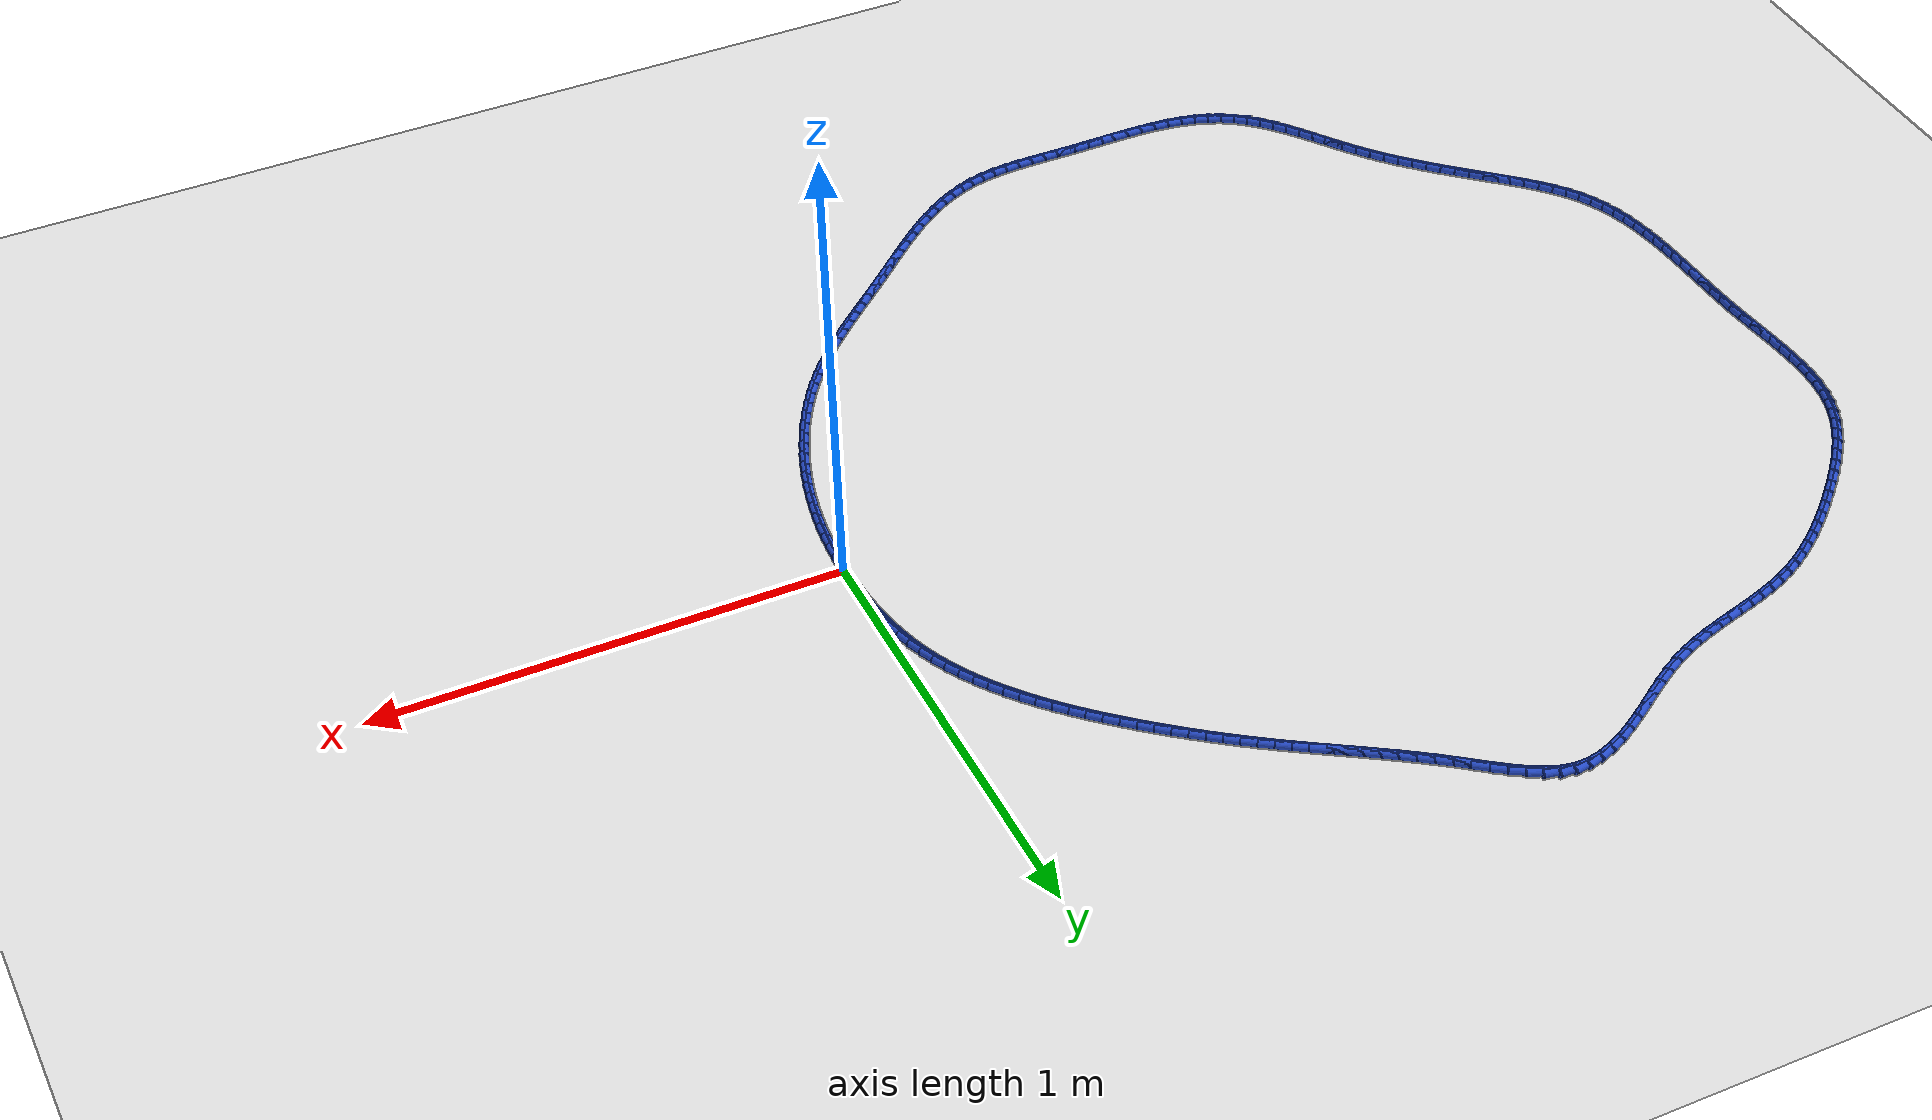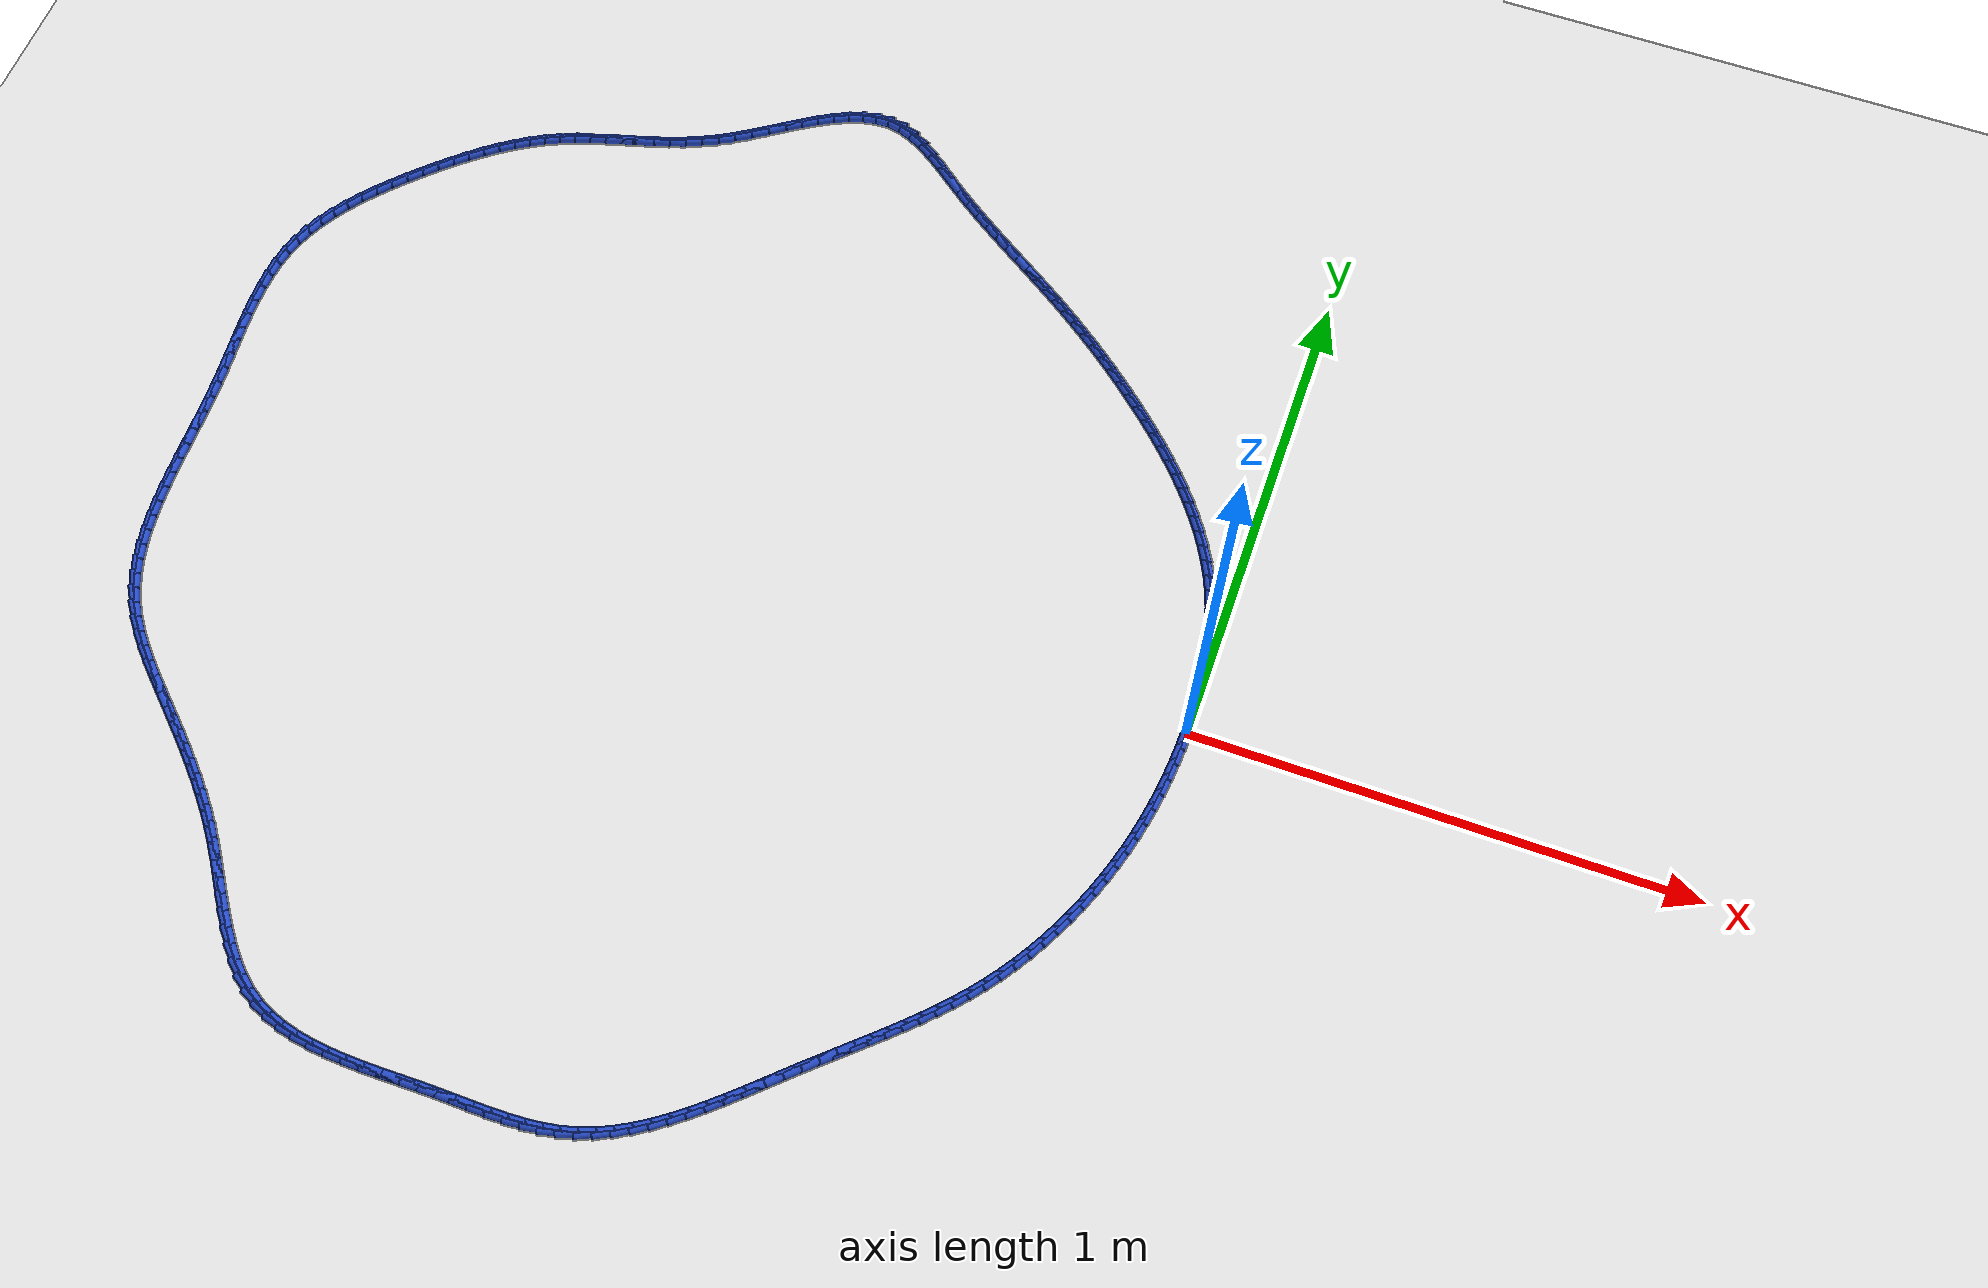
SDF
<sdf version="1.6">
 <world name="default">
  <light name="sun" type="directional">
   <pose>0 0 10 0 -0 0</pose>
   <diffuse>0.8 0.8 0.8 1</diffuse>
   <specular>0.2 0.2 0.2 1</specular>
   <attenuation>
    <range>1000</range>
    <constant>0.9</constant>
    <linear>0.01</linear>
    <quadratic>0.001</quadratic>
   </attenuation>
   <direction>-0.5 0.1 -0.9</direction>
  </light>
  <model name="ground_plane">
   <static>1</static>
   <link name="link">
    <collision name="collision">
     <geometry><plane><normal>0 0 1</normal><size>100 100</size></plane></geometry>
     <surface><friction><ode><mu>100</mu><mu2>50</mu2></ode></friction></surface>
    </collision>
    <visual name="visual">
     <cast_shadows>0</cast_shadows>
     <geometry><plane><normal>0 0 1</normal><size>100 100</size></plane></geometry>
     <material>
      <script><uri>file://media/materials/scripts/gazebo.material</uri><name>Gazebo/WhiteGlow</name></script>
     </material>
    </visual>
   </link>
  </model>
  <gravity>0 0 -9.8</gravity>
  <magnetic_field>6e-06 2.3e-05 -4.2e-05</magnetic_field>
  <atmosphere type="adiabatic"/>
  <physics name="default_physics" default="0" type="ode">
   <max_step_size>0.001</max_step_size>
   <real_time_factor>1</real_time_factor>
   <real_time_update_rate>1000</real_time_update_rate>
  </physics>
  <scene><ambient>0.4 0.4 0.4 1</ambient><background>0.7 0.7 0.7 1</background><shadows>1</shadows></scene>
  <spherical_coordinates>
   <surface_model>EARTH_WGS84</surface_model>
   <latitude_deg>0</latitude_deg>
   <longitude_deg>0</longitude_deg>
   <elevation>0</elevation>
   <heading_deg>0</heading_deg>
  </spherical_coordinates>
  <model name="line">
   <link name="link_0">
    <pose>3.642919299551295e-17 2.7755575615628914e-17 0.01 0 1.57 1.570233959817323</pose>
    <collision name="collision">
     <geometry><cylinder><radius>0.01</radius><length>0.08</length></cylinder></geometry>
    </collision>
    <visual name="visual">
     <material>
      <script><name>Gazebo/Blue</name><uri>file://media/materials/scripts/gazebo.material</uri></script>
     </material>
     <geometry><cylinder><radius>0.01</radius><length>0.08</length></cylinder></geometry>
    </visual>
   </link>
   <link name="link_1">
    <pose>1.9030973392364642e-05 0.03384084084776214 0.01 0 1.57 -1.5405084652589922</pose>
    <collision name="collision">
     <geometry><cylinder><radius>0.01</radius><length>0.08</length></cylinder></geometry>
    </collision>
    <visual name="visual">
     <material>
      <script><name>Gazebo/Blue</name><uri>file://media/materials/scripts/gazebo.material</uri></script>
     </material>
     <geometry><cylinder><radius>0.01</radius><length>0.08</length></cylinder></geometry>
    </visual>
   </link>
   <link name="link_2">
    <pose>-0.0010073156019435555 0.06771687774421273 0.01 0 1.57 -1.5070896232701272</pose>
    <collision name="collision">
     <geometry><cylinder><radius>0.01</radius><length>0.08</length></cylinder></geometry>
    </collision>
    <visual name="visual">
     <material>
      <script><name>Gazebo/Blue</name><uri>file://media/materials/scripts/gazebo.material</uri></script>
     </material>
     <geometry><cylinder><radius>0.01</radius><length>0.08</length></cylinder></geometry>
    </visual>
   </link>
   <link name="link_3">
    <pose>-0.0031645359947151067 0.10153280436257073 0.01 0 1.57 -1.4709059110682532</pose>
    <collision name="collision">
     <geometry><cylinder><radius>0.01</radius><length>0.08</length></cylinder></geometry>
    </collision>
    <visual name="visual">
     <material>
      <script><name>Gazebo/Blue</name><uri>file://media/materials/scripts/gazebo.material</uri></script>
     </material>
     <geometry><cylinder><radius>0.01</radius><length>0.08</length></cylinder></geometry>
    </visual>
   </link>
   <link name="link_4">
    <pose>-0.006538126473629663 0.1351933143760551 0.01 0 1.57 -1.4317565542293285</pose>
    <collision name="collision">
     <geometry><cylinder><radius>0.01</radius><length>0.08</length></cylinder></geometry>
    </collision>
    <visual name="visual">
     <material>
      <script><name>Gazebo/Blue</name><uri>file://media/materials/scripts/gazebo.material</uri></script>
     </material>
     <geometry><cylinder><radius>0.01</radius><length>0.08</length></cylinder></geometry>
    </visual>
   </link>
   <link name="link_5">
    <pose>-0.011213583307394599 0.16860310145788487 0.01 0 1.57 -1.3894434722486968</pose>
    <collision name="collision">
     <geometry><cylinder><radius>0.01</radius><length>0.08</length></cylinder></geometry>
    </collision>
    <visual name="visual">
     <material>
      <script><name>Gazebo/Blue</name><uri>file://media/materials/scripts/gazebo.material</uri></script>
     </material>
     <geometry><cylinder><radius>0.01</radius><length>0.08</length></cylinder></geometry>
    </visual>
   </link>
   <link name="link_6">
    <pose>-0.017276402764717286 0.20166685928127898 0.01 0 1.57 -1.3437813333467756</pose>
    <collision name="collision">
     <geometry><cylinder><radius>0.01</radius><length>0.08</length></cylinder></geometry>
    </collision>
    <visual name="visual">
     <material>
      <script><name>Gazebo/Blue</name><uri>file://media/materials/scripts/gazebo.material</uri></script>
     </material>
     <geometry><cylinder><radius>0.01</radius><length>0.08</length></cylinder></geometry>
    </visual>
   </link>
   <link name="link_7">
    <pose>-0.024812081114305114 0.2342892815194565 0.01 0 1.57 -1.2946109575999925</pose>
    <collision name="collision">
     <geometry><cylinder><radius>0.01</radius><length>0.08</length></cylinder></geometry>
    </collision>
    <visual name="visual">
     <material>
      <script><name>Gazebo/Blue</name><uri>file://media/materials/scripts/gazebo.material</uri></script>
     </material>
     <geometry><cylinder><radius>0.01</radius><length>0.08</length></cylinder></geometry>
    </visual>
   </link>
   <link name="link_8">
    <pose>-0.03390611462486543 0.2663750618456363 0.01 0 1.57 -1.2418163340584838</pose>
    <collision name="collision">
     <geometry><cylinder><radius>0.01</radius><length>0.08</length></cylinder></geometry>
    </collision>
    <visual name="visual">
     <material>
      <script><name>Gazebo/Blue</name><uri>file://media/materials/scripts/gazebo.material</uri></script>
     </material>
     <geometry><cylinder><radius>0.01</radius><length>0.08</length></cylinder></geometry>
    </visual>
   </link>
   <link name="link_9">
    <pose>-0.04464399956510562 0.2978288939330373 0.01 0 1.57 -1.1856470532846257</pose>
    <collision name="collision">
     <geometry><cylinder><radius>0.01</radius><length>0.08</length></cylinder></geometry>
    </collision>
    <visual name="visual">
     <material>
      <script><name>Gazebo/Blue</name><uri>file://media/materials/scripts/gazebo.material</uri></script>
     </material>
     <geometry><cylinder><radius>0.01</radius><length>0.08</length></cylinder></geometry>
    </visual>
   </link>
   <link name="link_10">
    <pose>-0.057102476147381294 0.3285605294937687 0.01 0 1.57 -1.1300614869389403</pose>
    <collision name="collision">
     <geometry><cylinder><radius>0.01</radius><length>0.08</length></cylinder></geometry>
    </collision>
    <visual name="visual">
     <material>
      <script><name>Gazebo/Blue</name><uri>file://media/materials/scripts/gazebo.material</uri></script>
     </material>
     <geometry><cylinder><radius>0.01</radius><length>0.08</length></cylinder></geometry>
    </visual>
   </link>
   <link name="link_11">
    <pose>-0.07124545831440758 0.35854489566101083 0.01 0 1.57 -1.0779402547479906</pose>
    <collision name="collision">
     <geometry><cylinder><radius>0.01</radius><length>0.08</length></cylinder></geometry>
    </collision>
    <visual name="visual">
     <material>
      <script><name>Gazebo/Blue</name><uri>file://media/materials/scripts/gazebo.material</uri></script>
     </material>
     <geometry><cylinder><radius>0.01</radius><length>0.08</length></cylinder></geometry>
    </visual>
   </link>
   <link name="link_12">
    <pose>-0.08695846034180377 0.3878022080573279 0.01 0 1.57 -1.0294471504644</pose>
    <collision name="collision">
     <geometry><cylinder><radius>0.01</radius><length>0.08</length></cylinder></geometry>
    </collision>
    <visual name="visual">
     <material>
      <script><name>Gazebo/Blue</name><uri>file://media/materials/scripts/gazebo.material</uri></script>
     </material>
     <geometry><cylinder><radius>0.01</radius><length>0.08</length></cylinder></geometry>
    </visual>
   </link>
   <link name="link_13">
    <pose>-0.10412541307795481 0.4163535969906417 0.01 0 1.57 -0.9846069180359244</pose>
    <collision name="collision">
     <geometry><cylinder><radius>0.01</radius><length>0.08</length></cylinder></geometry>
    </collision>
    <visual name="visual">
     <material>
      <script><name>Gazebo/Blue</name><uri>file://media/materials/scripts/gazebo.material</uri></script>
     </material>
     <geometry><cylinder><radius>0.01</radius><length>0.08</length></cylinder></geometry>
    </visual>
   </link>
   <link name="link_14">
    <pose>-0.12263024737124555 0.44422019276887326 0.01 0 1.57 -0.9433792235251794</pose>
    <collision name="collision">
     <geometry><cylinder><radius>0.01</radius><length>0.08</length></cylinder></geometry>
    </collision>
    <visual name="visual">
     <material>
      <script><name>Gazebo/Blue</name><uri>file://media/materials/scripts/gazebo.material</uri></script>
     </material>
     <geometry><cylinder><radius>0.01</radius><length>0.08</length></cylinder></geometry>
    </visual>
   </link>
   <link name="link_15">
    <pose>-0.14235689407006086 0.47142312569994416 0.01 0 1.57 -0.9056772445537078</pose>
    <collision name="collision">
     <geometry><cylinder><radius>0.01</radius><length>0.08</length></cylinder></geometry>
    </collision>
    <visual name="visual">
     <material>
      <script><name>Gazebo/Blue</name><uri>file://media/materials/scripts/gazebo.material</uri></script>
     </material>
     <geometry><cylinder><radius>0.01</radius><length>0.08</length></cylinder></geometry>
    </visual>
   </link>
   <link name="link_16">
    <pose>-0.1631892840227857 0.49798352609177604 0.01 0 1.57 -0.8713841653663587</pose>
    <collision name="collision">
     <geometry><cylinder><radius>0.01</radius><length>0.08</length></cylinder></geometry>
    </collision>
    <visual name="visual">
     <material>
      <script><name>Gazebo/Blue</name><uri>file://media/materials/scripts/gazebo.material</uri></script>
     </material>
     <geometry><cylinder><radius>0.01</radius><length>0.08</length></cylinder></geometry>
    </visual>
   </link>
   <link name="link_17">
    <pose>-0.185011348077805 0.5239225242522902 0.01 0 1.57 -0.8403669960143396</pose>
    <collision name="collision">
     <geometry><cylinder><radius>0.01</radius><length>0.08</length></cylinder></geometry>
    </collision>
    <visual name="visual">
     <material>
      <script><name>Gazebo/Blue</name><uri>file://media/materials/scripts/gazebo.material</uri></script>
     </material>
     <geometry><cylinder><radius>0.01</radius><length>0.08</length></cylinder></geometry>
    </visual>
   </link>
   <link name="link_18">
    <pose>-0.20770701708350353 0.5492612504894079 0.01 0 1.57 -0.812487660986767</pose>
    <collision name="collision">
     <geometry><cylinder><radius>0.01</radius><length>0.08</length></cylinder></geometry>
    </collision>
    <visual name="visual">
     <material>
      <script><name>Gazebo/Blue</name><uri>file://media/materials/scripts/gazebo.material</uri></script>
     </material>
     <geometry><cylinder><radius>0.01</radius><length>0.08</length></cylinder></geometry>
    </visual>
   </link>
   <link name="link_19">
    <pose>-0.23116022188826635 0.5740208351110511 0.01 0 1.57 -0.7876116209407888</pose>
    <collision name="collision">
     <geometry><cylinder><radius>0.01</radius><length>0.08</length></cylinder></geometry>
    </collision>
    <visual name="visual">
     <material>
      <script><name>Gazebo/Blue</name><uri>file://media/materials/scripts/gazebo.material</uri></script>
     </material>
     <geometry><cylinder><radius>0.01</radius><length>0.08</length></cylinder></geometry>
    </visual>
   </link>
   <link name="link_20">
    <pose>-0.2552548933404783 0.5982224084251409 0.01 0 1.57 -0.7656144477485122</pose>
    <collision name="collision">
     <geometry><cylinder><radius>0.01</radius><length>0.08</length></cylinder></geometry>
    </collision>
    <visual name="visual">
     <material>
      <script><name>Gazebo/Blue</name><uri>file://media/materials/scripts/gazebo.material</uri></script>
     </material>
     <geometry><cylinder><radius>0.01</radius><length>0.08</length></cylinder></geometry>
    </visual>
   </link>
   <link name="link_21">
    <pose>-0.2798749622885242 0.6218871007395987 0.01 0 1.57 -0.7463868220054993</pose>
    <collision name="collision">
     <geometry><cylinder><radius>0.01</radius><length>0.08</length></cylinder></geometry>
    </collision>
    <visual name="visual">
     <material>
      <script><name>Gazebo/Blue</name><uri>file://media/materials/scripts/gazebo.material</uri></script>
     </material>
     <geometry><cylinder><radius>0.01</radius><length>0.08</length></cylinder></geometry>
    </visual>
   </link>
   <link name="link_22">
    <pose>-0.304904359580789 0.6450360423623459 0.01 0 1.57 -0.7295826748881026</pose>
    <collision name="collision">
     <geometry><cylinder><radius>0.01</radius><length>0.08</length></cylinder></geometry>
    </collision>
    <visual name="visual">
     <material>
      <script><name>Gazebo/Blue</name><uri>file://media/materials/scripts/gazebo.material</uri></script>
     </material>
     <geometry><cylinder><radius>0.01</radius><length>0.08</length></cylinder></geometry>
    </visual>
   </link>
   <link name="link_23">
    <pose>-0.3302377116236706 0.6676882709718833 0.01 0 1.57 -0.7136197527650386</pose>
    <collision name="collision">
     <geometry><cylinder><radius>0.01</radius><length>0.08</length></cylinder></geometry>
    </collision>
    <visual name="visual">
     <material>
      <script><name>Gazebo/Blue</name><uri>file://media/materials/scripts/gazebo.material</uri></script>
     </material>
     <geometry><cylinder><radius>0.01</radius><length>0.08</length></cylinder></geometry>
    </visual>
   </link>
   <link name="link_24">
    <pose>-0.35583363456779177 0.6898503043930251 0.01 0 1.57 -0.6979207393844671</pose>
    <collision name="collision">
     <geometry><cylinder><radius>0.01</radius><length>0.08</length></cylinder></geometry>
    </collision>
    <visual name="visual">
     <material>
      <script><name>Gazebo/Blue</name><uri>file://media/materials/scripts/gazebo.material</uri></script>
     </material>
     <geometry><cylinder><radius>0.01</radius><length>0.08</length></cylinder></geometry>
    </visual>
   </link>
   <link name="link_25">
    <pose>-0.38167443776278376 0.7115240247798469 0.01 0 1.57 -0.68247843453223</pose>
    <collision name="collision">
     <geometry><cylinder><radius>0.01</radius><length>0.08</length></cylinder></geometry>
    </collision>
    <visual name="visual">
     <material>
      <script><name>Gazebo/Blue</name><uri>file://media/materials/scripts/gazebo.material</uri></script>
     </material>
     <geometry><cylinder><radius>0.01</radius><length>0.08</length></cylinder></geometry>
    </visual>
   </link>
   <link name="link_26">
    <pose>-0.4077424690165581 0.7327113067619049 0.01 0 1.57 -0.6672861522883738</pose>
    <collision name="collision">
     <geometry><cylinder><radius>0.01</radius><length>0.08</length></cylinder></geometry>
    </collision>
    <visual name="visual">
     <material>
      <script><name>Gazebo/Blue</name><uri>file://media/materials/scripts/gazebo.material</uri></script>
     </material>
     <geometry><cylinder><radius>0.01</radius><length>0.08</length></cylinder></geometry>
    </visual>
   </link>
   <link name="link_27">
    <pose>-0.4340200761370263 0.753414024968755 0.01 0 1.57 -0.6523368322119392</pose>
    <collision name="collision">
     <geometry><cylinder><radius>0.01</radius><length>0.08</length></cylinder></geometry>
    </collision>
    <visual name="visual">
     <material>
      <script><name>Gazebo/Blue</name><uri>file://media/materials/scripts/gazebo.material</uri></script>
     </material>
     <geometry><cylinder><radius>0.01</radius><length>0.08</length></cylinder></geometry>
    </visual>
   </link>
   <link name="link_28">
    <pose>-0.4604896069321003 0.7736340540299536 0.01 0 1.57 -0.6376230663312977</pose>
    <collision name="collision">
     <geometry><cylinder><radius>0.01</radius><length>0.08</length></cylinder></geometry>
    </collision>
    <visual name="visual">
     <material>
      <script><name>Gazebo/Blue</name><uri>file://media/materials/scripts/gazebo.material</uri></script>
     </material>
     <geometry><cylinder><radius>0.01</radius><length>0.08</length></cylinder></geometry>
    </visual>
   </link>
   <link name="link_29">
    <pose>-0.4871334092096914 0.7933732685750569 0.01 0 1.57 -0.6231371224895905</pose>
    <collision name="collision">
     <geometry><cylinder><radius>0.01</radius><length>0.08</length></cylinder></geometry>
    </collision>
    <visual name="visual">
     <material>
      <script><name>Gazebo/Blue</name><uri>file://media/materials/scripts/gazebo.material</uri></script>
     </material>
     <geometry><cylinder><radius>0.01</radius><length>0.08</length></cylinder></geometry>
    </visual>
   </link>
   <link name="link_30">
    <pose>-0.5139338307777117 0.8126335432336214 0.01 0 1.57 -0.6088783524560051</pose>
    <collision name="collision">
     <geometry><cylinder><radius>0.01</radius><length>0.08</length></cylinder></geometry>
    </collision>
    <visual name="visual">
     <material>
      <script><name>Gazebo/Blue</name><uri>file://media/materials/scripts/gazebo.material</uri></script>
     </material>
     <geometry><cylinder><radius>0.01</radius><length>0.08</length></cylinder></geometry>
    </visual>
   </link>
   <link name="link_31">
    <pose>-0.5408732568803185 0.8314170745424095 0.01 0 1.57 -0.5958637551251947</pose>
    <collision name="collision">
     <geometry><cylinder><radius>0.01</radius><length>0.08</length></cylinder></geometry>
    </collision>
    <visual name="visual">
     <material>
      <script><name>Gazebo/Blue</name><uri>file://media/materials/scripts/gazebo.material</uri></script>
     </material>
     <geometry><cylinder><radius>0.01</radius><length>0.08</length></cylinder></geometry>
    </visual>
   </link>
   <link name="link_32">
    <pose>-0.5679391808949069 0.8497699829107975 0.01 0 1.57 -0.58621183312326</pose>
    <collision name="collision">
     <geometry><cylinder><radius>0.01</radius><length>0.08</length></cylinder></geometry>
    </collision>
    <visual name="visual">
     <material>
      <script><name>Gazebo/Blue</name><uri>file://media/materials/scripts/gazebo.material</uri></script>
     </material>
     <geometry><cylinder><radius>0.01</radius><length>0.08</length></cylinder></geometry>
    </visual>
   </link>
   <link name="link_33">
    <pose>-0.5951293443169947 0.8678265103797044 0.01 0 1.57 -0.5802576577408157</pose>
    <collision name="collision">
     <geometry><cylinder><radius>0.01</radius><length>0.08</length></cylinder></geometry>
    </collision>
    <visual name="visual">
     <material>
      <script><name>Gazebo/Blue</name><uri>file://media/materials/scripts/gazebo.material</uri></script>
     </material>
     <geometry><cylinder><radius>0.01</radius><length>0.08</length></cylinder></geometry>
    </visual>
   </link>
   <link name="link_34">
    <pose>-0.6224427130974622 0.8857314278503656 0.01 0 1.57 -0.5780383491943036</pose>
    <collision name="collision">
     <geometry><cylinder><radius>0.01</radius><length>0.08</length></cylinder></geometry>
    </collision>
    <visual name="visual">
     <material>
      <script><name>Gazebo/Blue</name><uri>file://media/materials/scripts/gazebo.material</uri></script>
     </material>
     <geometry><cylinder><radius>0.01</radius><length>0.08</length></cylinder></geometry>
    </visual>
   </link>
   <link name="link_35">
    <pose>-0.6498782531871893 0.9036295062240172 0.01 0 1.57 -0.579536351483204</pose>
    <collision name="collision">
     <geometry><cylinder><radius>0.01</radius><length>0.08</length></cylinder></geometry>
    </collision>
    <visual name="visual">
     <material>
      <script><name>Gazebo/Blue</name><uri>file://media/materials/scripts/gazebo.material</uri></script>
     </material>
     <geometry><cylinder><radius>0.01</radius><length>0.08</length></cylinder></geometry>
    </visual>
   </link>
   <link name="link_36">
    <pose>-0.677434930537056 0.9216655164018948 0.01 0 1.57 -0.584681567155481</pose>
    <collision name="collision">
     <geometry><cylinder><radius>0.01</radius><length>0.08</length></cylinder></geometry>
    </collision>
    <visual name="visual">
     <material>
      <script><name>Gazebo/Blue</name><uri>file://media/materials/scripts/gazebo.material</uri></script>
     </material>
     <geometry><cylinder><radius>0.01</radius><length>0.08</length></cylinder></geometry>
    </visual>
   </link>
   <link name="link_37">
    <pose>-0.7051117110979419 0.9399842292852337 0.01 0 1.57 -0.5933538135637033</pose>
    <collision name="collision">
     <geometry><cylinder><radius>0.01</radius><length>0.08</length></cylinder></geometry>
    </collision>
    <visual name="visual">
     <material>
      <script><name>Gazebo/Blue</name><uri>file://media/materials/scripts/gazebo.material</uri></script>
     </material>
     <geometry><cylinder><radius>0.01</radius><length>0.08</length></cylinder></geometry>
    </visual>
   </link>
   <link name="link_38">
    <pose>-0.7329075608207278 0.9587304157752703 0.01 0 1.57 -0.6053856303098277</pose>
    <collision name="collision">
     <geometry><cylinder><radius>0.01</radius><length>0.08</length></cylinder></geometry>
    </collision>
    <visual name="visual">
     <material>
      <script><name>Gazebo/Blue</name><uri>file://media/materials/scripts/gazebo.material</uri></script>
     </material>
     <geometry><cylinder><radius>0.01</radius><length>0.08</length></cylinder></geometry>
    </visual>
   </link>
   <link name="link_39">
    <pose>-0.7608214456562933 0.9780488467732402 0.01 0 1.57 -0.6205656041561253</pose>
    <collision name="collision">
     <geometry><cylinder><radius>0.01</radius><length>0.08</length></cylinder></geometry>
    </collision>
    <visual name="visual">
     <material>
      <script><name>Gazebo/Blue</name><uri>file://media/materials/scripts/gazebo.material</uri></script>
     </material>
     <geometry><cylinder><radius>0.01</radius><length>0.08</length></cylinder></geometry>
    </visual>
   </link>
   <link name="link_40">
    <pose>-0.7888523315555183 0.9980842931803787 0.01 0 1.57 -0.6386424512458385</pose>
    <collision name="collision">
     <geometry><cylinder><radius>0.01</radius><length>0.08</length></cylinder></geometry>
    </collision>
    <visual name="visual">
     <material>
      <script><name>Gazebo/Blue</name><uri>file://media/materials/scripts/gazebo.material</uri></script>
     </material>
     <geometry><cylinder><radius>0.01</radius><length>0.08</length></cylinder></geometry>
    </visual>
   </link>
   <link name="link_41">
    <pose>-0.816999184469283 1.0189815258979222 0.01 0 1.57 -0.6575045595633787</pose>
    <collision name="collision">
     <geometry><cylinder><radius>0.01</radius><length>0.08</length></cylinder></geometry>
    </collision>
    <visual name="visual">
     <material>
      <script><name>Gazebo/Blue</name><uri>file://media/materials/scripts/gazebo.material</uri></script>
     </material>
     <geometry><cylinder><radius>0.01</radius><length>0.08</length></cylinder></geometry>
    </visual>
   </link>
   <link name="link_42">
    <pose>-0.8452613478158196 1.0408031405037799 0.01 0 1.57 -0.6597538097990658</pose>
    <collision name="collision">
     <geometry><cylinder><radius>0.01</radius><length>0.08</length></cylinder></geometry>
    </collision>
    <visual name="visual">
     <material>
      <script><name>Gazebo/Blue</name><uri>file://media/materials/scripts/gazebo.material</uri></script>
     </material>
     <geometry><cylinder><radius>0.01</radius><length>0.08</length></cylinder></geometry>
    </visual>
   </link>
   <link name="link_43">
    <pose>-0.873641810225049 1.0628181634186311 0.01 0 1.57 -0.6357151832701613</pose>
    <collision name="collision">
     <geometry><cylinder><radius>0.01</radius><length>0.08</length></cylinder></geometry>
    </collision>
    <visual name="visual">
     <material>
      <script><name>Gazebo/Blue</name><uri>file://media/materials/scripts/gazebo.material</uri></script>
     </material>
     <geometry><cylinder><radius>0.01</radius><length>0.08</length></cylinder></geometry>
    </visual>
   </link>
   <link name="link_44">
    <pose>-0.9021456015183954 1.08385124999183 0.01 0 1.57 -0.5827325616523604</pose>
    <collision name="collision">
     <geometry><cylinder><radius>0.01</radius><length>0.08</length></cylinder></geometry>
    </collision>
    <visual name="visual">
     <material>
      <script><name>Gazebo/Blue</name><uri>file://media/materials/scripts/gazebo.material</uri></script>
     </material>
     <geometry><cylinder><radius>0.01</radius><length>0.08</length></cylinder></geometry>
    </visual>
   </link>
   <link name="link_45">
    <pose>-0.9307777739596247 1.1027221698348026 0.01 0 1.57 -0.4950012499214727</pose>
    <collision name="collision">
     <geometry><cylinder><radius>0.01</radius><length>0.08</length></cylinder></geometry>
    </collision>
    <visual name="visual">
     <material>
      <script><name>Gazebo/Blue</name><uri>file://media/materials/scripts/gazebo.material</uri></script>
     </material>
     <geometry><cylinder><radius>0.01</radius><length>0.08</length></cylinder></geometry>
    </visual>
   </link>
   <link name="link_46">
    <pose>-0.9595433798125022 1.1182506925589735 0.01 0 1.57 -0.3638222263117783</pose>
    <collision name="collision">
     <geometry><cylinder><radius>0.01</radius><length>0.08</length></cylinder></geometry>
    </collision>
    <visual name="visual">
     <material>
      <script><name>Gazebo/Blue</name><uri>file://media/materials/scripts/gazebo.material</uri></script>
     </material>
     <geometry><cylinder><radius>0.01</radius><length>0.08</length></cylinder></geometry>
    </visual>
   </link>
   <link name="link_47">
    <pose>-0.9884474713407929 1.1292565877757679 0.01 0 1.57 -0.1816693596775093</pose>
    <collision name="collision">
     <geometry><cylinder><radius>0.01</radius><length>0.08</length></cylinder></geometry>
    </collision>
    <visual name="visual">
     <material>
      <script><name>Gazebo/Blue</name><uri>file://media/materials/scripts/gazebo.material</uri></script>
     </material>
     <geometry><cylinder><radius>0.01</radius><length>0.08</length></cylinder></geometry>
    </visual>
   </link>
   <link name="link_48">
    <pose>-1.0174952653235396 1.1345925133369614 0.01 0 1.57 0.02013924699540519</pose>
    <collision name="collision">
     <geometry><cylinder><radius>0.01</radius><length>0.08</length></cylinder></geometry>
    </collision>
    <visual name="visual">
     <material>
      <script><name>Gazebo/Blue</name><uri>file://media/materials/scripts/gazebo.material</uri></script>
     </material>
     <geometry><cylinder><radius>0.01</radius><length>0.08</length></cylinder></geometry>
    </visual>
   </link>
   <link name="link_49">
    <pose>-1.0466964466362036 1.134004344013409 0.01 0 1.57 0.19464441656322196</pose>
    <collision name="collision">
     <geometry><cylinder><radius>0.01</radius><length>0.08</length></cylinder></geometry>
    </collision>
    <visual name="visual">
     <material>
      <script><name>Gazebo/Blue</name><uri>file://media/materials/scripts/gazebo.material</uri></script>
     </material>
     <geometry><cylinder><radius>0.01</radius><length>0.08</length></cylinder></geometry>
    </visual>
   </link>
   <link name="link_50">
    <pose>-1.0760655850857805 1.1282145009810196 0.01 0 1.57 0.33294182814942536</pose>
    <collision name="collision">
     <geometry><cylinder><radius>0.01</radius><length>0.08</length></cylinder></geometry>
    </collision>
    <visual name="visual">
     <material>
      <script><name>Gazebo/Blue</name><uri>file://media/materials/scripts/gazebo.material</uri></script>
     </material>
     <geometry><cylinder><radius>0.01</radius><length>0.08</length></cylinder></geometry>
    </visual>
   </link>
   <link name="link_51">
    <pose>-1.1056174985695253 1.117995001126438 0.01 0 1.57 0.43646254641301574</pose>
    <collision name="collision">
     <geometry><cylinder><radius>0.01</radius><length>0.08</length></cylinder></geometry>
    </collision>
    <visual name="visual">
     <material>
      <script><name>Gazebo/Blue</name><uri>file://media/materials/scripts/gazebo.material</uri></script>
     </material>
     <geometry><cylinder><radius>0.01</radius><length>0.08</length></cylinder></geometry>
    </visual>
   </link>
   <link name="link_52">
    <pose>-1.1353670049846938 1.1041178613363076 0.01 0 1.57 0.5100839713462348</pose>
    <collision name="collision">
     <geometry><cylinder><radius>0.01</radius><length>0.08</length></cylinder></geometry>
    </collision>
    <visual name="visual">
     <material>
      <script><name>Gazebo/Blue</name><uri>file://media/materials/scripts/gazebo.material</uri></script>
     </material>
     <geometry><cylinder><radius>0.01</radius><length>0.08</length></cylinder></geometry>
    </visual>
   </link>
   <link name="link_53">
    <pose>-1.1653289222285417 1.087355098497274 0.01 0 1.57 0.5587934895889223</pose>
    <collision name="collision">
     <geometry><cylinder><radius>0.01</radius><length>0.08</length></cylinder></geometry>
    </collision>
    <visual name="visual">
     <material>
      <script><name>Gazebo/Blue</name><uri>file://media/materials/scripts/gazebo.material</uri></script>
     </material>
     <geometry><cylinder><radius>0.01</radius><length>0.08</length></cylinder></geometry>
    </visual>
   </link>
   <link name="link_54">
    <pose>-1.1955180681983235 1.0684787294959799 0.01 0 1.57 0.586419737218822</pose>
    <collision name="collision">
     <geometry><cylinder><radius>0.01</radius><length>0.08</length></cylinder></geometry>
    </collision>
    <visual name="visual">
     <material>
      <script><name>Gazebo/Blue</name><uri>file://media/materials/scripts/gazebo.material</uri></script>
     </material>
     <geometry><cylinder><radius>0.01</radius><length>0.08</length></cylinder></geometry>
    </visual>
   </link>
   <link name="link_55">
    <pose>-1.225949260791296 1.0482607712190717 0.01 0 1.57 0.5953841174515219</pose>
    <collision name="collision">
     <geometry><cylinder><radius>0.01</radius><length>0.08</length></cylinder></geometry>
    </collision>
    <visual name="visual">
     <material>
      <script><name>Gazebo/Blue</name><uri>file://media/materials/scripts/gazebo.material</uri></script>
     </material>
     <geometry><cylinder><radius>0.01</radius><length>0.08</length></cylinder></geometry>
    </visual>
   </link>
   <link name="link_56">
    <pose>-1.256637317904714 1.0274732405531923 0.01 0 1.57 0.5867775291602454</pose>
    <collision name="collision">
     <geometry><cylinder><radius>0.01</radius><length>0.08</length></cylinder></geometry>
    </collision>
    <visual name="visual">
     <material>
      <script><name>Gazebo/Blue</name><uri>file://media/materials/scripts/gazebo.material</uri></script>
     </material>
     <geometry><cylinder><radius>0.01</radius><length>0.08</length></cylinder></geometry>
    </visual>
   </link>
   <link name="link_57">
    <pose>-1.2875970574358322 1.0068881543849864 0.01 0 1.57 0.560477921617894</pose>
    <collision name="collision">
     <geometry><cylinder><radius>0.01</radius><length>0.08</length></cylinder></geometry>
    </collision>
    <visual name="visual">
     <material>
      <script><name>Gazebo/Blue</name><uri>file://media/materials/scripts/gazebo.material</uri></script>
     </material>
     <geometry><cylinder><radius>0.01</radius><length>0.08</length></cylinder></geometry>
    </visual>
   </link>
   <link name="link_58">
    <pose>-1.318843297281907 0.9872775296010987 0.01 0 1.57 0.5152417630013832</pose>
    <collision name="collision">
     <geometry><cylinder><radius>0.01</radius><length>0.08</length></cylinder></geometry>
    </collision>
    <visual name="visual">
     <material>
      <script><name>Gazebo/Blue</name><uri>file://media/materials/scripts/gazebo.material</uri></script>
     </material>
     <geometry><cylinder><radius>0.01</radius><length>0.08</length></cylinder></geometry>
    </visual>
   </link>
   <link name="link_59">
    <pose>-1.3503908553401938 0.9694133830881732 0.01 0 1.57 0.4533265770896093</pose>
    <collision name="collision">
     <geometry><cylinder><radius>0.01</radius><length>0.08</length></cylinder></geometry>
    </collision>
    <visual name="visual">
     <material>
      <script><name>Gazebo/Blue</name><uri>file://media/materials/scripts/gazebo.material</uri></script>
     </material>
     <geometry><cylinder><radius>0.01</radius><length>0.08</length></cylinder></geometry>
    </visual>
   </link>
   <link name="link_60">
    <pose>-1.3822378140079319 0.95389867564105 0.01 0 1.57 0.39497438391797124</pose>
    <collision name="collision">
     <geometry><cylinder><radius>0.01</radius><length>0.08</length></cylinder></geometry>
    </collision>
    <visual name="visual">
     <material>
      <script><name>Gazebo/Blue</name><uri>file://media/materials/scripts/gazebo.material</uri></script>
     </material>
     <geometry><cylinder><radius>0.01</radius><length>0.08</length></cylinder></geometry>
    </visual>
   </link>
   <link name="link_61">
    <pose>-1.414302574950923 0.9405314615363625 0.01 0 1.57 0.3476762622930825</pose>
    <collision name="collision">
     <geometry><cylinder><radius>0.01</radius><length>0.08</length></cylinder></geometry>
    </collision>
    <visual name="visual">
     <material>
      <script><name>Gazebo/Blue</name><uri>file://media/materials/scripts/gazebo.material</uri></script>
     </material>
     <geometry><cylinder><radius>0.01</radius><length>0.08</length></cylinder></geometry>
    </visual>
   </link>
   <link name="link_62">
    <pose>-1.4464798512812636 0.9288705016740093 0.01 0 1.57 0.31243288606901987</pose>
    <collision name="collision">
     <geometry><cylinder><radius>0.01</radius><length>0.08</length></cylinder></geometry>
    </collision>
    <visual name="visual">
     <material>
      <script><name>Gazebo/Blue</name><uri>file://media/materials/scripts/gazebo.material</uri></script>
     </material>
     <geometry><cylinder><radius>0.01</radius><length>0.08</length></cylinder></geometry>
    </visual>
   </link>
   <link name="link_63">
    <pose>-1.478664352214446 0.9184745175917847 0.01 0 1.57 0.289922283530248</pose>
    <collision name="collision">
     <geometry><cylinder><radius>0.01</radius><length>0.08</length></cylinder></geometry>
    </collision>
    <visual name="visual">
     <material>
      <script><name>Gazebo/Blue</name><uri>file://media/materials/scripts/gazebo.material</uri></script>
     </material>
     <geometry><cylinder><radius>0.01</radius><length>0.08</length></cylinder></geometry>
    </visual>
   </link>
   <link name="link_64">
    <pose>-1.510750786965962 0.9089022308274816 0.01 0 1.57 0.280629994271288</pose>
    <collision name="collision">
     <geometry><cylinder><radius>0.01</radius><length>0.08</length></cylinder></geometry>
    </collision>
    <visual name="visual">
     <material>
      <script><name>Gazebo/Blue</name><uri>file://media/materials/scripts/gazebo.material</uri></script>
     </material>
     <geometry><cylinder><radius>0.01</radius><length>0.08</length></cylinder></geometry>
    </visual>
   </link>
   <link name="link_65">
    <pose>-1.5426338647513045 0.8997123629188934 0.01 0 1.57 0.28494720110951344</pose>
    <collision name="collision">
     <geometry><cylinder><radius>0.01</radius><length>0.08</length></cylinder></geometry>
    </collision>
    <visual name="visual">
     <material>
      <script><name>Gazebo/Blue</name><uri>file://media/materials/scripts/gazebo.material</uri></script>
     </material>
     <geometry><cylinder><radius>0.01</radius><length>0.08</length></cylinder></geometry>
    </visual>
   </link>
   <link name="link_66">
    <pose>-1.5742082947859648 0.8904636354038135 0.01 0 1.57 0.3032126371316894</pose>
    <collision name="collision">
     <geometry><cylinder><radius>0.01</radius><length>0.08</length></cylinder></geometry>
    </collision>
    <visual name="visual">
     <material>
      <script><name>Gazebo/Blue</name><uri>file://media/materials/scripts/gazebo.material</uri></script>
     </material>
     <geometry><cylinder><radius>0.01</radius><length>0.08</length></cylinder></geometry>
    </visual>
   </link>
   <link name="link_67">
    <pose>-1.6053687862854358 0.8807147698200348 0.01 0 1.57 0.33568131168886234</pose>
    <collision name="collision">
     <geometry><cylinder><radius>0.01</radius><length>0.08</length></cylinder></geometry>
    </collision>
    <visual name="visual">
     <material>
      <script><name>Gazebo/Blue</name><uri>file://media/materials/scripts/gazebo.material</uri></script>
     </material>
     <geometry><cylinder><radius>0.01</radius><length>0.08</length></cylinder></geometry>
    </visual>
   </link>
   <link name="link_68">
    <pose>-1.63601004846521 0.8700244877053516 0.01 0 1.57 0.3824084698986068</pose>
    <collision name="collision">
     <geometry><cylinder><radius>0.01</radius><length>0.08</length></cylinder></geometry>
    </collision>
    <visual name="visual">
     <material>
      <script><name>Gazebo/Blue</name><uri>file://media/materials/scripts/gazebo.material</uri></script>
     </material>
     <geometry><cylinder><radius>0.01</radius><length>0.08</length></cylinder></geometry>
    </visual>
   </link>
   <link name="link_69">
    <pose>-1.666026790540779 0.8579515105975564 0.01 0 1.57 0.44217697061646555</pose>
    <collision name="collision">
     <geometry><cylinder><radius>0.01</radius><length>0.08</length></cylinder></geometry>
    </collision>
    <visual name="visual">
     <material>
      <script><name>Gazebo/Blue</name><uri>file://media/materials/scripts/gazebo.material</uri></script>
     </material>
     <geometry><cylinder><radius>0.01</radius><length>0.08</length></cylinder></geometry>
    </visual>
   </link>
   <link name="link_70">
    <pose>-1.6953209063977133 0.844082424650987 0.01 0 1.57 0.5035948965340085</pose>
    <collision name="collision">
     <geometry><cylinder><radius>0.01</radius><length>0.08</length></cylinder></geometry>
    </collision>
    <visual name="visual">
     <material>
      <script><name>Gazebo/Blue</name><uri>file://media/materials/scripts/gazebo.material</uri></script>
     </material>
     <geometry><cylinder><radius>0.01</radius><length>0.08</length></cylinder></geometry>
    </visual>
   </link>
   <link name="link_71">
    <pose>-1.7238824204854988 0.8283456165957505 0.01 0 1.57 0.5591934578957851</pose>
    <collision name="collision">
     <geometry><cylinder><radius>0.01</radius><length>0.08</length></cylinder></geometry>
    </collision>
    <visual name="visual">
     <material>
      <script><name>Gazebo/Blue</name><uri>file://media/materials/scripts/gazebo.material</uri></script>
     </material>
     <geometry><cylinder><radius>0.01</radius><length>0.08</length></cylinder></geometry>
    </visual>
   </link>
   <link name="link_72">
    <pose>-1.751760483485701 0.8108987849837469 0.01 0 1.57 0.6088395163548921</pose>
    <collision name="collision">
     <geometry><cylinder><radius>0.01</radius><length>0.08</length></cylinder></geometry>
    </collision>
    <visual name="visual">
     <material>
      <script><name>Gazebo/Blue</name><uri>file://media/materials/scripts/gazebo.material</uri></script>
     </material>
     <geometry><cylinder><radius>0.01</radius><length>0.08</length></cylinder></geometry>
    </visual>
   </link>
   <link name="link_73">
    <pose>-1.779005338602812 0.791903865545777 0.01 0 1.57 0.652670693244233</pose>
    <collision name="collision">
     <geometry><cylinder><radius>0.01</radius><length>0.08</length></cylinder></geometry>
    </collision>
    <visual name="visual">
     <material>
      <script><name>Gazebo/Blue</name><uri>file://media/materials/scripts/gazebo.material</uri></script>
     </material>
     <geometry><cylinder><radius>0.01</radius><length>0.08</length></cylinder></geometry>
    </visual>
   </link>
   <link name="link_74">
    <pose>-1.8056672290413247 0.771522794012641 0.01 0 1.57 0.6909085673088882</pose>
    <collision name="collision">
     <geometry><cylinder><radius>0.01</radius><length>0.08</length></cylinder></geometry>
    </collision>
    <visual name="visual">
     <material>
      <script><name>Gazebo/Blue</name><uri>file://media/materials/scripts/gazebo.material</uri></script>
     </material>
     <geometry><cylinder><radius>0.01</radius><length>0.08</length></cylinder></geometry>
    </visual>
   </link>
   <link name="link_75">
    <pose>-1.8317963980057312 0.7499175061151394 0.01 0 1.57 0.7238147894607163</pose>
    <collision name="collision">
     <geometry><cylinder><radius>0.01</radius><length>0.08</length></cylinder></geometry>
    </collision>
    <visual name="visual">
     <material>
      <script><name>Gazebo/Blue</name><uri>file://media/materials/scripts/gazebo.material</uri></script>
     </material>
     <geometry><cylinder><radius>0.01</radius><length>0.08</length></cylinder></geometry>
    </visual>
   </link>
   <link name="link_76">
    <pose>-1.8574430887005253 0.7272499375840727 0.01 0 1.57 0.7516581589905312</pose>
    <collision name="collision">
     <geometry><cylinder><radius>0.01</radius><length>0.08</length></cylinder></geometry>
    </collision>
    <visual name="visual">
     <material>
      <script><name>Gazebo/Blue</name><uri>file://media/materials/scripts/gazebo.material</uri></script>
     </material>
     <geometry><cylinder><radius>0.01</radius><length>0.08</length></cylinder></geometry>
    </visual>
   </link>
   <link name="link_77">
    <pose>-1.8826575443301985 0.7036820241502411 0.01 0 1.57 0.7746973485571419</pose>
    <collision name="collision">
     <geometry><cylinder><radius>0.01</radius><length>0.08</length></cylinder></geometry>
    </collision>
    <visual name="visual">
     <material>
      <script><name>Gazebo/Blue</name><uri>file://media/materials/scripts/gazebo.material</uri></script>
     </material>
     <geometry><cylinder><radius>0.01</radius><length>0.08</length></cylinder></geometry>
    </visual>
   </link>
   <link name="link_78">
    <pose>-1.9074898119739137 0.6793756006135165 0.01 0 1.57 0.7957583543262888</pose>
    <collision name="collision">
     <geometry><cylinder><radius>0.01</radius><length>0.08</length></cylinder></geometry>
    </collision>
    <visual name="visual">
     <material>
      <script><name>Gazebo/Blue</name><uri>file://media/materials/scripts/gazebo.material</uri></script>
     </material>
     <geometry><cylinder><radius>0.01</radius><length>0.08</length></cylinder></geometry>
    </visual>
   </link>
   <link name="link_79">
    <pose>-1.931905270820337 0.6544489295906067 0.01 0 1.57 0.8217496124324785</pose>
    <collision name="collision">
     <geometry><cylinder><radius>0.01</radius><length>0.08</length></cylinder></geometry>
    </collision>
    <visual name="visual">
     <material>
      <script><name>Gazebo/Blue</name><uri>file://media/materials/scripts/gazebo.material</uri></script>
     </material>
     <geometry><cylinder><radius>0.01</radius><length>0.08</length></cylinder></geometry>
    </visual>
   </link>
   <link name="link_80">
    <pose>-1.9556528506716304 0.6289088835093414 0.01 0 1.57 0.854114407242088</pose>
    <collision name="collision">
     <geometry><cylinder><radius>0.01</radius><length>0.08</length></cylinder></geometry>
    </collision>
    <visual name="visual">
     <material>
      <script><name>Gazebo/Blue</name><uri>file://media/materials/scripts/gazebo.material</uri></script>
     </material>
     <geometry><cylinder><radius>0.01</radius><length>0.08</length></cylinder></geometry>
    </visual>
   </link>
   <link name="link_81">
    <pose>-1.978447386795913 0.6027447889100414 0.01 0 1.57 0.8933927188373583</pose>
    <collision name="collision">
     <geometry><cylinder><radius>0.01</radius><length>0.08</length></cylinder></geometry>
    </collision>
    <visual name="visual">
     <material>
      <script><name>Gazebo/Blue</name><uri>file://media/materials/scripts/gazebo.material</uri></script>
     </material>
     <geometry><cylinder><radius>0.01</radius><length>0.08</length></cylinder></geometry>
    </visual>
   </link>
   <link name="link_82">
    <pose>-2.0000037144613048 0.5759459723330285 0.01 0 1.57 0.9402499541824688</pose>
    <collision name="collision">
     <geometry><cylinder><radius>0.01</radius><length>0.08</length></cylinder></geometry>
    </collision>
    <visual name="visual">
     <material>
      <script><name>Gazebo/Blue</name><uri>file://media/materials/scripts/gazebo.material</uri></script>
     </material>
     <geometry><cylinder><radius>0.01</radius><length>0.08</length></cylinder></geometry>
    </visual>
   </link>
   <link name="link_83">
    <pose>-2.020036668935926 0.5485017603186237 0.01 0 1.57 0.9954416307006323</pose>
    <collision name="collision">
     <geometry><cylinder><radius>0.01</radius><length>0.08</length></cylinder></geometry>
    </collision>
    <visual name="visual">
     <material>
      <script><name>Gazebo/Blue</name><uri>file://media/materials/scripts/gazebo.material</uri></script>
     </material>
     <geometry><cylinder><radius>0.01</radius><length>0.08</length></cylinder></geometry>
    </visual>
   </link>
   <link name="link_84">
    <pose>-2.0382610854878953 0.5204014794071488 0.01 0 1.57 1.0597476678402529</pose>
    <collision name="collision">
     <geometry><cylinder><radius>0.01</radius><length>0.08</length></cylinder></geometry>
    </collision>
    <visual name="visual">
     <material>
      <script><name>Gazebo/Blue</name><uri>file://media/materials/scripts/gazebo.material</uri></script>
     </material>
     <geometry><cylinder><radius>0.01</radius><length>0.08</length></cylinder></geometry>
    </visual>
   </link>
   <link name="link_85">
    <pose>-2.054391799385333 0.49163445613892415 0.01 0 1.57 1.133859416235579</pose>
    <collision name="collision">
     <geometry><cylinder><radius>0.01</radius><length>0.08</length></cylinder></geometry>
    </collision>
    <visual name="visual">
     <material>
      <script><name>Gazebo/Blue</name><uri>file://media/materials/scripts/gazebo.material</uri></script>
     </material>
     <geometry><cylinder><radius>0.01</radius><length>0.08</length></cylinder></geometry>
    </visual>
   </link>
   <link name="link_86">
    <pose>-2.0681436458963574 0.46219001705427154 0.01 0 1.57 1.2182046653109042</pose>
    <collision name="collision">
     <geometry><cylinder><radius>0.01</radius><length>0.08</length></cylinder></geometry>
    </collision>
    <visual name="visual">
     <material>
      <script><name>Gazebo/Blue</name><uri>file://media/materials/scripts/gazebo.material</uri></script>
     </material>
     <geometry><cylinder><radius>0.01</radius><length>0.08</length></cylinder></geometry>
    </visual>
   </link>
   <link name="link_87">
    <pose>-2.079231460289089 0.43205748869351235 0.01 0 1.57 1.3106681438810828</pose>
    <collision name="collision">
     <geometry><cylinder><radius>0.01</radius><length>0.08</length></cylinder></geometry>
    </collision>
    <visual name="visual">
     <material>
      <script><name>Gazebo/Blue</name><uri>file://media/materials/scripts/gazebo.material</uri></script>
     </material>
     <geometry><cylinder><radius>0.01</radius><length>0.08</length></cylinder></geometry>
    </visual>
   </link>
   <link name="link_88">
    <pose>-2.0874358032344955 0.4012324965084866 0.01 0 1.57 1.3974873219055268</pose>
    <collision name="collision">
     <geometry><cylinder><radius>0.01</radius><length>0.08</length></cylinder></geometry>
    </collision>
    <visual name="visual">
     <material>
      <script><name>Gazebo/Blue</name><uri>file://media/materials/scripts/gazebo.material</uri></script>
     </material>
     <geometry><cylinder><radius>0.01</radius><length>0.08</length></cylinder></geometry>
    </visual>
   </link>
   <link name="link_89">
    <pose>-2.09294730133179 0.3697499653525889 0.01 0 1.57 1.472419461701992</pose>
    <collision name="collision">
     <geometry><cylinder><radius>0.01</radius><length>0.08</length></cylinder></geometry>
    </collision>
    <visual name="visual">
     <material>
      <script><name>Gazebo/Blue</name><uri>file://media/materials/scripts/gazebo.material</uri></script>
     </material>
     <geometry><cylinder><radius>0.01</radius><length>0.08</length></cylinder></geometry>
    </visual>
   </link>
   <link name="link_90">
    <pose>-2.0961144403581535 0.3376599487958346 0.01 0 1.57 1.5349253558592544</pose>
    <collision name="collision">
     <geometry><cylinder><radius>0.01</radius><length>0.08</length></cylinder></geometry>
    </collision>
    <visual name="visual">
     <material>
      <script><name>Gazebo/Blue</name><uri>file://media/materials/scripts/gazebo.material</uri></script>
     </material>
     <geometry><cylinder><radius>0.01</radius><length>0.08</length></cylinder></geometry>
    </visual>
   </link>
   <link name="link_91">
    <pose>-2.0972860374427515 0.30501253216394897 0.01 0 1.57 -1.5564666915634682</pose>
    <collision name="collision">
     <geometry><cylinder><radius>0.01</radius><length>0.08</length></cylinder></geometry>
    </collision>
    <visual name="visual">
     <material>
      <script><name>Gazebo/Blue</name><uri>file://media/materials/scripts/gazebo.material</uri></script>
     </material>
     <geometry><cylinder><radius>0.01</radius><length>0.08</length></cylinder></geometry>
    </visual>
   </link>
   <link name="link_92">
    <pose>-2.0968109097147534 0.27185780078265737 0.01 0 1.57 -1.51809503911049</pose>
    <collision name="collision">
     <geometry><cylinder><radius>0.01</radius><length>0.08</length></cylinder></geometry>
    </collision>
    <visual name="visual">
     <material>
      <script><name>Gazebo/Blue</name><uri>file://media/materials/scripts/gazebo.material</uri></script>
     </material>
     <geometry><cylinder><radius>0.01</radius><length>0.08</length></cylinder></geometry>
    </visual>
   </link>
   <link name="link_93">
    <pose>-2.095037874303325 0.23824583997768498 0.01 0 1.57 -1.4909488869938654</pose>
    <collision name="collision">
     <geometry><cylinder><radius>0.01</radius><length>0.08</length></cylinder></geometry>
    </collision>
    <visual name="visual">
     <material>
      <script><name>Gazebo/Blue</name><uri>file://media/materials/scripts/gazebo.material</uri></script>
     </material>
     <geometry><cylinder><radius>0.01</radius><length>0.08</length></cylinder></geometry>
    </visual>
   </link>
   <link name="link_94">
    <pose>-2.0923157483376347 0.2042267350747572 0.01 0 1.57 -1.4744472321491544</pose>
    <collision name="collision">
     <geometry><cylinder><radius>0.01</radius><length>0.08</length></cylinder></geometry>
    </collision>
    <visual name="visual">
     <material>
      <script><name>Gazebo/Blue</name><uri>file://media/materials/scripts/gazebo.material</uri></script>
     </material>
     <geometry><cylinder><radius>0.01</radius><length>0.08</length></cylinder></geometry>
    </visual>
   </link>
   <link name="link_95">
    <pose>-2.0889933489468486 0.16985057139959936 0.01 0 1.57 -1.4681156856893767</pose>
    <collision name="collision">
     <geometry><cylinder><radius>0.01</radius><length>0.08</length></cylinder></geometry>
    </collision>
    <visual name="visual">
     <material>
      <script><name>Gazebo/Blue</name><uri>file://media/materials/scripts/gazebo.material</uri></script>
     </material>
     <geometry><cylinder><radius>0.01</radius><length>0.08</length></cylinder></geometry>
    </visual>
   </link>
   <link name="link_96">
    <pose>-2.085419493260136 0.1351674342779372 0.01 0 1.57 -1.4716238155051418</pose>
    <collision name="collision">
     <geometry><cylinder><radius>0.01</radius><length>0.08</length></cylinder></geometry>
    </collision>
    <visual name="visual">
     <material>
      <script><name>Gazebo/Blue</name><uri>file://media/materials/scripts/gazebo.material</uri></script>
     </material>
     <geometry><cylinder><radius>0.01</radius><length>0.08</length></cylinder></geometry>
    </visual>
   </link>
   <link name="link_97">
    <pose>-2.081942998406663 0.10022740903549524 0.01 0 1.57 -1.4847902325735955</pose>
    <collision name="collision">
     <geometry><cylinder><radius>0.01</radius><length>0.08</length></cylinder></geometry>
    </collision>
    <visual name="visual">
     <material>
      <script><name>Gazebo/Blue</name><uri>file://media/materials/scripts/gazebo.material</uri></script>
     </material>
     <geometry><cylinder><radius>0.01</radius><length>0.08</length></cylinder></geometry>
    </visual>
   </link>
   <link name="link_98">
    <pose>-2.0789126815155963 0.06508058099799927 0.01 0 1.57 -1.5057254777299764</pose>
    <collision name="collision">
     <geometry><cylinder><radius>0.01</radius><length>0.08</length></cylinder></geometry>
    </collision>
    <visual name="visual">
     <material>
      <script><name>Gazebo/Blue</name><uri>file://media/materials/scripts/gazebo.material</uri></script>
     </material>
     <geometry><cylinder><radius>0.01</radius><length>0.08</length></cylinder></geometry>
    </visual>
   </link>
   <link name="link_99">
    <pose>-2.076612486736325 0.029781404965039598 0.01 0 1.57 -1.523644288274695</pose>
    <collision name="collision">
     <geometry><cylinder><radius>0.01</radius><length>0.08</length></cylinder></geometry>
    </collision>
    <visual name="visual">
     <material>
      <script><name>Gazebo/Blue</name><uri>file://media/materials/scripts/gazebo.material</uri></script>
     </material>
     <geometry><cylinder><radius>0.01</radius><length>0.08</length></cylinder></geometry>
    </visual>
   </link>
   <link name="link_100">
    <pose>-2.0749434217937957 -0.005589871850615254 0.01 0 1.57 -1.534692976717922</pose>
    <collision name="collision">
     <geometry><cylinder><radius>0.01</radius><length>0.08</length></cylinder></geometry>
    </collision>
    <visual name="visual">
     <material>
      <script><name>Gazebo/Blue</name><uri>file://media/materials/scripts/gazebo.material</uri></script>
     </material>
     <geometry><cylinder><radius>0.01</radius><length>0.08</length></cylinder></geometry>
    </visual>
   </link>
   <link name="link_101">
    <pose>-2.0736664799341002 -0.04094357165958111 0.01 0 1.57 -1.5389164289456263</pose>
    <collision name="collision">
     <geometry><cylinder><radius>0.01</radius><length>0.08</length></cylinder></geometry>
    </collision>
    <visual name="visual">
     <material>
      <script><name>Gazebo/Blue</name><uri>file://media/materials/scripts/gazebo.material</uri></script>
     </material>
     <geometry><cylinder><radius>0.01</radius><length>0.08</length></cylinder></geometry>
    </visual>
   </link>
   <link name="link_102">
    <pose>-2.072542446492661 -0.07619000266879705 0.01 0 1.57 -1.5362777188165193</pose>
    <collision name="collision">
     <geometry><cylinder><radius>0.01</radius><length>0.08</length></cylinder></geometry>
    </collision>
    <visual name="visual">
     <material>
      <script><name>Gazebo/Blue</name><uri>file://media/materials/scripts/gazebo.material</uri></script>
     </material>
     <geometry><cylinder><radius>0.01</radius><length>0.08</length></cylinder></geometry>
    </visual>
   </link>
   <link name="link_103">
    <pose>-2.0713321068049004 -0.1112394730852024 0.01 0 1.57 -1.5266439094920232</pose>
    <collision name="collision">
     <geometry><cylinder><radius>0.01</radius><length>0.08</length></cylinder></geometry>
    </collision>
    <visual name="visual">
     <material>
      <script><name>Gazebo/Blue</name><uri>file://media/materials/scripts/gazebo.material</uri></script>
     </material>
     <geometry><cylinder><radius>0.01</radius><length>0.08</length></cylinder></geometry>
    </visual>
   </link>
   <link name="link_104">
    <pose>-2.0697962462062396 -0.14600229111573615 0.01 0 1.57 -1.5097842827070018</pose>
    <collision name="collision">
     <geometry><cylinder><radius>0.01</radius><length>0.08</length></cylinder></geometry>
    </collision>
    <visual name="visual">
     <material>
      <script><name>Gazebo/Blue</name><uri>file://media/materials/scripts/gazebo.material</uri></script>
     </material>
     <geometry><cylinder><radius>0.01</radius><length>0.08</length></cylinder></geometry>
    </visual>
   </link>
   <link name="link_105">
    <pose>-2.0676956500321024 -0.18038876496733752 0.01 0 1.57 -1.4853764806179743</pose>
    <collision name="collision">
     <geometry><cylinder><radius>0.01</radius><length>0.08</length></cylinder></geometry>
    </collision>
    <visual name="visual">
     <material>
      <script><name>Gazebo/Blue</name><uri>file://media/materials/scripts/gazebo.material</uri></script>
     </material>
     <geometry><cylinder><radius>0.01</radius><length>0.08</length></cylinder></geometry>
    </visual>
   </link>
   <link name="link_106">
    <pose>-2.064791103617908 -0.21430920284694555 0.01 0 1.57 -1.453023914822367</pose>
    <collision name="collision">
     <geometry><cylinder><radius>0.01</radius><length>0.08</length></cylinder></geometry>
    </collision>
    <visual name="visual">
     <material>
      <script><name>Gazebo/Blue</name><uri>file://media/materials/scripts/gazebo.material</uri></script>
     </material>
     <geometry><cylinder><radius>0.01</radius><length>0.08</length></cylinder></geometry>
    </visual>
   </link>
   <link name="link_107">
    <pose>-2.060843392299082 -0.24767391296149954 0.01 0 1.57 -1.4122899376955553</pose>
    <collision name="collision">
     <geometry><cylinder><radius>0.01</radius><length>0.08</length></cylinder></geometry>
    </collision>
    <visual name="visual">
     <material>
      <script><name>Gazebo/Blue</name><uri>file://media/materials/scripts/gazebo.material</uri></script>
     </material>
     <geometry><cylinder><radius>0.01</radius><length>0.08</length></cylinder></geometry>
    </visual>
   </link>
   <link name="link_108">
    <pose>-2.0556133014110443 -0.28039320351793856 0.01 0 1.57 -1.362756068350395</pose>
    <collision name="collision">
     <geometry><cylinder><radius>0.01</radius><length>0.08</length></cylinder></geometry>
    </collision>
    <visual name="visual">
     <material>
      <script><name>Gazebo/Blue</name><uri>file://media/materials/scripts/gazebo.material</uri></script>
     </material>
     <geometry><cylinder><radius>0.01</radius><length>0.08</length></cylinder></geometry>
    </visual>
   </link>
   <link name="link_109">
    <pose>-2.0488616162892175 -0.3123773827232018 0.01 0 1.57 -1.3041117224252987</pose>
    <collision name="collision">
     <geometry><cylinder><radius>0.01</radius><length>0.08</length></cylinder></geometry>
    </collision>
    <visual name="visual">
     <material>
      <script><name>Gazebo/Blue</name><uri>file://media/materials/scripts/gazebo.material</uri></script>
     </material>
     <geometry><cylinder><radius>0.01</radius><length>0.08</length></cylinder></geometry>
    </visual>
   </link>
   <link name="link_110">
    <pose>-2.0403491222690233 -0.34353675878422835 0.01 0 1.57 -1.2362789809003452</pose>
    <collision name="collision">
     <geometry><cylinder><radius>0.01</radius><length>0.08</length></cylinder></geometry>
    </collision>
    <visual name="visual">
     <material>
      <script><name>Gazebo/Blue</name><uri>file://media/materials/scripts/gazebo.material</uri></script>
     </material>
     <geometry><cylinder><radius>0.01</radius><length>0.08</length></cylinder></geometry>
    </visual>
   </link>
   <link name="link_111">
    <pose>-2.0298366046858844 -0.3737816399079574 0.01 0 1.57 -1.15956476094815</pose>
    <collision name="collision">
     <geometry><cylinder><radius>0.01</radius><length>0.08</length></cylinder></geometry>
    </collision>
    <visual name="visual">
     <material>
      <script><name>Gazebo/Blue</name><uri>file://media/materials/scripts/gazebo.material</uri></script>
     </material>
     <geometry><cylinder><radius>0.01</radius><length>0.08</length></cylinder></geometry>
    </visual>
   </link>
   <link name="link_112">
    <pose>-2.0170848488752227 -0.40302233430132806 0.01 0 1.57 -1.0748127150763933</pose>
    <collision name="collision">
     <geometry><cylinder><radius>0.01</radius><length>0.08</length></cylinder></geometry>
    </collision>
    <visual name="visual">
     <material>
      <script><name>Gazebo/Blue</name><uri>file://media/materials/scripts/gazebo.material</uri></script>
     </material>
     <geometry><cylinder><radius>0.01</radius><length>0.08</length></cylinder></geometry>
    </visual>
   </link>
   <link name="link_113">
    <pose>-2.001854640172461 -0.43116915017127955 0.01 0 1.57 -0.9856146404977786</pose>
    <collision name="collision">
     <geometry><cylinder><radius>0.01</radius><length>0.08</length></cylinder></geometry>
    </collision>
    <visual name="visual">
     <material>
      <script><name>Gazebo/Blue</name><uri>file://media/materials/scripts/gazebo.material</uri></script>
     </material>
     <geometry><cylinder><radius>0.01</radius><length>0.08</length></cylinder></geometry>
    </visual>
   </link>
   <link name="link_114">
    <pose>-1.9839735339199358 -0.45815544024462984 0.01 0 1.57 -0.9075027163497561</pose>
    <collision name="collision">
     <geometry><cylinder><radius>0.01</radius><length>0.08</length></cylinder></geometry>
    </collision>
    <visual name="visual">
     <material>
      <script><name>Gazebo/Blue</name><uri>file://media/materials/scripts/gazebo.material</uri></script>
     </material>
     <geometry><cylinder><radius>0.01</radius><length>0.08</length></cylinder></geometry>
    </visual>
   </link>
   <link name="link_115">
    <pose>-1.9637230397320546 -0.48407123176015265 0.01 0 1.57 -0.8457941318825607</pose>
    <collision name="collision">
     <geometry><cylinder><radius>0.01</radius><length>0.08</length></cylinder></geometry>
    </collision>
    <visual name="visual">
     <material>
      <script><name>Gazebo/Blue</name><uri>file://media/materials/scripts/gazebo.material</uri></script>
     </material>
     <geometry><cylinder><radius>0.01</radius><length>0.08</length></cylinder></geometry>
    </visual>
   </link>
   <link name="link_116">
    <pose>-1.9415736347070207 -0.5090717708346469 0.01 0 1.57 -0.7992734333436672</pose>
    <collision name="collision">
     <geometry><cylinder><radius>0.01</radius><length>0.08</length></cylinder></geometry>
    </collision>
    <visual name="visual">
     <material>
      <script><name>Gazebo/Blue</name><uri>file://media/materials/scripts/gazebo.material</uri></script>
     </material>
     <geometry><cylinder><radius>0.01</radius><length>0.08</length></cylinder></geometry>
    </visual>
   </link>
   <link name="link_117">
    <pose>-1.917996417267101 -0.5333125180242314 0.01 0 1.57 -0.766768201511137</pose>
    <collision name="collision">
     <geometry><cylinder><radius>0.01</radius><length>0.08</length></cylinder></geometry>
    </collision>
    <visual name="visual">
     <material>
      <script><name>Gazebo/Blue</name><uri>file://media/materials/scripts/gazebo.material</uri></script>
     </material>
     <geometry><cylinder><radius>0.01</radius><length>0.08</length></cylinder></geometry>
    </visual>
   </link>
   <link name="link_118">
    <pose>-1.8934624858345648 -0.5569489338850239 0.01 0 1.57 -0.7474136953929731</pose>
    <collision name="collision">
     <geometry><cylinder><radius>0.01</radius><length>0.08</length></cylinder></geometry>
    </collision>
    <visual name="visual">
     <material>
      <script><name>Gazebo/Blue</name><uri>file://media/materials/scripts/gazebo.material</uri></script>
     </material>
     <geometry><cylinder><radius>0.01</radius><length>0.08</length></cylinder></geometry>
    </visual>
   </link>
   <link name="link_119">
    <pose>-1.8684429388316812 -0.5801364789731421 0.01 0 1.57 -0.740666915526459</pose>
    <collision name="collision">
     <geometry><cylinder><radius>0.01</radius><length>0.08</length></cylinder></geometry>
    </collision>
    <visual name="visual">
     <material>
      <script><name>Gazebo/Blue</name><uri>file://media/materials/scripts/gazebo.material</uri></script>
     </material>
     <geometry><cylinder><radius>0.01</radius><length>0.08</length></cylinder></geometry>
    </visual>
   </link>
   <link name="link_120">
    <pose>-1.8434033179525808 -0.6030305354492963 0.01 0 1.57 -0.7428197144372886</pose>
    <collision name="collision">
     <geometry><cylinder><radius>0.01</radius><length>0.08</length></cylinder></geometry>
    </collision>
    <visual name="visual">
     <material>
      <script><name>Gazebo/Blue</name><uri>file://media/materials/scripts/gazebo.material</uri></script>
     </material>
     <geometry><cylinder><radius>0.01</radius><length>0.08</length></cylinder></geometry>
    </visual>
   </link>
   <link name="link_121">
    <pose>-1.8186249151188476 -0.625783886042347 0.01 0 1.57 -0.7494962252402626</pose>
    <collision name="collision">
     <geometry><cylinder><radius>0.01</radius><length>0.08</length></cylinder></geometry>
    </collision>
    <visual name="visual">
     <material>
      <script><name>Gazebo/Blue</name><uri>file://media/materials/scripts/gazebo.material</uri></script>
     </material>
     <geometry><cylinder><radius>0.01</radius><length>0.08</length></cylinder></geometry>
    </visual>
   </link>
   <link name="link_122">
    <pose>-1.7941665853535498 -0.6485461752978585 0.01 0 1.57 -0.7604743352403701</pose>
    <collision name="collision">
     <geometry><cylinder><radius>0.01</radius><length>0.08</length></cylinder></geometry>
    </collision>
    <visual name="visual">
     <material>
      <script><name>Gazebo/Blue</name><uri>file://media/materials/scripts/gazebo.material</uri></script>
     </material>
     <geometry><cylinder><radius>0.01</radius><length>0.08</length></cylinder></geometry>
    </visual>
   </link>
   <link name="link_123">
    <pose>-1.7700739044903981 -0.6714668604159937 0.01 0 1.57 -0.7757434217971474</pose>
    <collision name="collision">
     <geometry><cylinder><radius>0.01</radius><length>0.08</length></cylinder></geometry>
    </collision>
    <visual name="visual">
     <material>
      <script><name>Gazebo/Blue</name><uri>file://media/materials/scripts/gazebo.material</uri></script>
     </material>
     <geometry><cylinder><radius>0.01</radius><length>0.08</length></cylinder></geometry>
    </visual>
   </link>
   <link name="link_124">
    <pose>-1.7463924483631024 -0.6946953985969148 0.01 0 1.57 -0.7952291817999287</pose>
    <collision name="collision">
     <geometry><cylinder><radius>0.01</radius><length>0.08</length></cylinder></geometry>
    </collision>
    <visual name="visual">
     <material>
      <script><name>Gazebo/Blue</name><uri>file://media/materials/scripts/gazebo.material</uri></script>
     </material>
     <geometry><cylinder><radius>0.01</radius><length>0.08</length></cylinder></geometry>
    </visual>
   </link>
   <link name="link_125">
    <pose>-1.7231677928053701 -0.718381247040784 0.01 0 1.57 -0.8187865858727852</pose>
    <collision name="collision">
     <geometry><cylinder><radius>0.01</radius><length>0.08</length></cylinder></geometry>
    </collision>
    <visual name="visual">
     <material>
      <script><name>Gazebo/Blue</name><uri>file://media/materials/scripts/gazebo.material</uri></script>
     </material>
     <geometry><cylinder><radius>0.01</radius><length>0.08</length></cylinder></geometry>
    </visual>
   </link>
   <link name="link_126">
    <pose>-1.7004455136509118 -0.7426738629477637 0.01 0 1.57 -0.8461939847146079</pose>
    <collision name="collision">
     <geometry><cylinder><radius>0.01</radius><length>0.08</length></cylinder></geometry>
    </collision>
    <visual name="visual">
     <material>
      <script><name>Gazebo/Blue</name><uri>file://media/materials/scripts/gazebo.material</uri></script>
     </material>
     <geometry><cylinder><radius>0.01</radius><length>0.08</length></cylinder></geometry>
    </visual>
   </link>
   <link name="link_127">
    <pose>-1.6782711867334368 -0.7677227035180167 0.01 0 1.57 -0.8771497994165618</pose>
    <collision name="collision">
     <geometry><cylinder><radius>0.01</radius><length>0.08</length></cylinder></geometry>
    </collision>
    <visual name="visual">
     <material>
      <script><name>Gazebo/Blue</name><uri>file://media/materials/scripts/gazebo.material</uri></script>
     </material>
     <geometry><cylinder><radius>0.01</radius><length>0.08</length></cylinder></geometry>
    </visual>
   </link>
   <link name="link_128">
    <pose>-1.656690387886654 -0.793677225951705 0.01 0 1.57 -0.9112242057142089</pose>
    <collision name="collision">
     <geometry><cylinder><radius>0.01</radius><length>0.08</length></cylinder></geometry>
    </collision>
    <visual name="visual">
     <material>
      <script><name>Gazebo/Blue</name><uri>file://media/materials/scripts/gazebo.material</uri></script>
     </material>
     <geometry><cylinder><radius>0.01</radius><length>0.08</length></cylinder></geometry>
    </visual>
   </link>
   <link name="link_129">
    <pose>-1.6357478669397354 -0.8206852132992687 0.01 0 1.57 -0.9423701717974627</pose>
    <collision name="collision">
     <geometry><cylinder><radius>0.01</radius><length>0.08</length></cylinder></geometry>
    </collision>
    <visual name="visual">
     <material>
      <script><name>Gazebo/Blue</name><uri>file://media/materials/scripts/gazebo.material</uri></script>
     </material>
     <geometry><cylinder><radius>0.01</radius><length>0.08</length></cylinder></geometry>
    </visual>
   </link>
   <link name="link_130">
    <pose>-1.6153911778962131 -0.8486974516733656 0.01 0 1.57 -0.9600876952361652</pose>
    <collision name="collision">
     <geometry><cylinder><radius>0.01</radius><length>0.08</length></cylinder></geometry>
    </collision>
    <visual name="visual">
     <material>
      <script><name>Gazebo/Blue</name><uri>file://media/materials/scripts/gazebo.material</uri></script>
     </material>
     <geometry><cylinder><radius>0.01</radius><length>0.08</length></cylinder></geometry>
    </visual>
   </link>
   <link name="link_131">
    <pose>-1.5953805676939106 -0.8772850923810697 0.01 0 1.57 -0.9637779672986069</pose>
    <collision name="collision">
     <geometry><cylinder><radius>0.01</radius><length>0.08</length></cylinder></geometry>
    </collision>
    <visual name="visual">
     <material>
      <script><name>Gazebo/Blue</name><uri>file://media/materials/scripts/gazebo.material</uri></script>
     </material>
     <geometry><cylinder><radius>0.01</radius><length>0.08</length></cylinder></geometry>
    </visual>
   </link>
   <link name="link_132">
    <pose>-1.5754549654873202 -0.9059760797500539 0.01 0 1.57 -0.953558357763635</pose>
    <collision name="collision">
     <geometry><cylinder><radius>0.01</radius><length>0.08</length></cylinder></geometry>
    </collision>
    <visual name="visual">
     <material>
      <script><name>Gazebo/Blue</name><uri>file://media/materials/scripts/gazebo.material</uri></script>
     </material>
     <geometry><cylinder><radius>0.01</radius><length>0.08</length></cylinder></geometry>
    </visual>
   </link>
   <link name="link_133">
    <pose>-1.5553533004309366 -0.9342983581079923 0.01 0 1.57 -0.9289819476766806</pose>
    <collision name="collision">
     <geometry><cylinder><radius>0.01</radius><length>0.08</length></cylinder></geometry>
    </collision>
    <visual name="visual">
     <material>
      <script><name>Gazebo/Blue</name><uri>file://media/materials/scripts/gazebo.material</uri></script>
     </material>
     <geometry><cylinder><radius>0.01</radius><length>0.08</length></cylinder></geometry>
    </visual>
   </link>
   <link name="link_134">
    <pose>-1.5348145016792518 -0.9617798717825583 0.01 0 1.57 -0.8890568759566296</pose>
    <collision name="collision">
     <geometry><cylinder><radius>0.01</radius><length>0.08</length></cylinder></geometry>
    </collision>
    <visual name="visual">
     <material>
      <script><name>Gazebo/Blue</name><uri>file://media/materials/scripts/gazebo.material</uri></script>
     </material>
     <geometry><cylinder><radius>0.01</radius><length>0.08</length></cylinder></geometry>
    </visual>
   </link>
   <link name="link_135">
    <pose>-1.5135774983867605 -0.9879485651014254 0.01 0 1.57 -0.8323266308561046</pose>
    <collision name="collision">
     <geometry><cylinder><radius>0.01</radius><length>0.08</length></cylinder></geometry>
    </collision>
    <visual name="visual">
     <material>
      <script><name>Gazebo/Blue</name><uri>file://media/materials/scripts/gazebo.material</uri></script>
     </material>
     <geometry><cylinder><radius>0.01</radius><length>0.08</length></cylinder></geometry>
    </visual>
   </link>
   <link name="link_136">
    <pose>-1.4913812197079541 -1.012332382392267 0.01 0 1.57 -0.757086891383281</pose>
    <collision name="collision">
     <geometry><cylinder><radius>0.01</radius><length>0.08</length></cylinder></geometry>
    </collision>
    <visual name="visual">
     <material>
      <script><name>Gazebo/Blue</name><uri>file://media/materials/scripts/gazebo.material</uri></script>
     </material>
     <geometry><cylinder><radius>0.01</radius><length>0.08</length></cylinder></geometry>
    </visual>
   </link>
   <link name="link_137">
    <pose>-1.4679645947973272 -1.0344592679827567 0.01 0 1.57 -0.6618623310233918</pose>
    <collision name="collision">
     <geometry><cylinder><radius>0.01</radius><length>0.08</length></cylinder></geometry>
    </collision>
    <visual name="visual">
     <material>
      <script><name>Gazebo/Blue</name><uri>file://media/materials/scripts/gazebo.material</uri></script>
     </material>
     <geometry><cylinder><radius>0.01</radius><length>0.08</length></cylinder></geometry>
    </visual>
   </link>
   <link name="link_138">
    <pose>-1.443066552809373 -1.0538571662005685 0.01 0 1.57 -0.5467680070899327</pose>
    <collision name="collision">
     <geometry><cylinder><radius>0.01</radius><length>0.08</length></cylinder></geometry>
    </collision>
    <visual name="visual">
     <material>
      <script><name>Gazebo/Blue</name><uri>file://media/materials/scripts/gazebo.material</uri></script>
     </material>
     <geometry><cylinder><radius>0.01</radius><length>0.08</length></cylinder></geometry>
    </visual>
   </link>
   <link name="link_139">
    <pose>-1.4164336039244778 -1.070067765952064 0.01 0 1.57 -0.4274583979008477</pose>
    <collision name="collision">
     <geometry><cylinder><radius>0.01</radius><length>0.08</length></cylinder></geometry>
    </collision>
    <visual name="visual">
     <material>
      <script><name>Gazebo/Blue</name><uri>file://media/materials/scripts/gazebo.material</uri></script>
     </material>
     <geometry><cylinder><radius>0.01</radius><length>0.08</length></cylinder></geometry>
    </visual>
   </link>
   <link name="link_140">
    <pose>-1.3880209439516802 -1.0830111081087015 0.01 0 1.57 -0.32205602162787905</pose>
    <collision name="collision">
     <geometry><cylinder><radius>0.01</radius><length>0.08</length></cylinder></geometry>
    </collision>
    <visual name="visual">
     <material>
      <script><name>Gazebo/Blue</name><uri>file://media/materials/scripts/gazebo.material</uri></script>
     </material>
     <geometry><cylinder><radius>0.01</radius><length>0.08</length></cylinder></geometry>
    </visual>
   </link>
   <link name="link_141">
    <pose>-1.3580135155707163 -1.0930237700354424 0.01 0 1.57 -0.2326121197201929</pose>
    <collision name="collision">
     <geometry><cylinder><radius>0.01</radius><length>0.08</length></cylinder></geometry>
    </collision>
    <visual name="visual">
     <material>
      <script><name>Gazebo/Blue</name><uri>file://media/materials/scripts/gazebo.material</uri></script>
     </material>
     <geometry><cylinder><radius>0.01</radius><length>0.08</length></cylinder></geometry>
    </visual>
   </link>
   <link name="link_142">
    <pose>-1.32660806694655 -1.1004637327203166 0.01 0 1.57 -0.15889953384746375</pose>
    <collision name="collision">
     <geometry><cylinder><radius>0.01</radius><length>0.08</length></cylinder></geometry>
    </collision>
    <visual name="visual">
     <material>
      <script><name>Gazebo/Blue</name><uri>file://media/materials/scripts/gazebo.material</uri></script>
     </material>
     <geometry><cylinder><radius>0.01</radius><length>0.08</length></cylinder></geometry>
    </visual>
   </link>
   <link name="link_143">
    <pose>-1.2940013462441473 -1.1056889771513532 0.01 0 1.57 -0.09988612282261042</pose>
    <collision name="collision">
     <geometry><cylinder><radius>0.01</radius><length>0.08</length></cylinder></geometry>
    </collision>
    <visual name="visual">
     <material>
      <script><name>Gazebo/Blue</name><uri>file://media/materials/scripts/gazebo.material</uri></script>
     </material>
     <geometry><cylinder><radius>0.01</radius><length>0.08</length></cylinder></geometry>
    </visual>
   </link>
   <link name="link_144">
    <pose>-1.260390101628472 -1.109057484316581 0.01 0 1.57 -0.054269845577993275</pose>
    <collision name="collision">
     <geometry><cylinder><radius>0.01</radius><length>0.08</length></cylinder></geometry>
    </collision>
    <visual name="visual">
     <material>
      <script><name>Gazebo/Blue</name><uri>file://media/materials/scripts/gazebo.material</uri></script>
     </material>
     <geometry><cylinder><radius>0.01</radius><length>0.08</length></cylinder></geometry>
    </visual>
   </link>
   <link name="link_145">
    <pose>-1.225971081264489 -1.1109272352040285 0.01 0 1.57 -0.02080700537237138</pose>
    <collision name="collision">
     <geometry><cylinder><radius>0.01</radius><length>0.08</length></cylinder></geometry>
    </collision>
    <visual name="visual">
     <material>
      <script><name>Gazebo/Blue</name><uri>file://media/materials/scripts/gazebo.material</uri></script>
     </material>
     <geometry><cylinder><radius>0.01</radius><length>0.08</length></cylinder></geometry>
    </visual>
   </link>
   <link name="link_146">
    <pose>-1.1909410333171637 -1.1116562108017256 0.01 0 1.57 0.001518399886939561</pose>
    <collision name="collision">
     <geometry><cylinder><radius>0.01</radius><length>0.08</length></cylinder></geometry>
    </collision>
    <visual name="visual">
     <material>
      <script><name>Gazebo/Blue</name><uri>file://media/materials/scripts/gazebo.material</uri></script>
     </material>
     <geometry><cylinder><radius>0.01</radius><length>0.08</length></cylinder></geometry>
    </visual>
   </link>
   <link name="link_147">
    <pose>-1.15549670595146 -1.1116023920977005 0.01 0 1.57 0.013420592758354978</pose>
    <collision name="collision">
     <geometry><cylinder><radius>0.01</radius><length>0.08</length></cylinder></geometry>
    </collision>
    <visual name="visual">
     <material>
      <script><name>Gazebo/Blue</name><uri>file://media/materials/scripts/gazebo.material</uri></script>
     </material>
     <geometry><cylinder><radius>0.01</radius><length>0.08</length></cylinder></geometry>
    </visual>
   </link>
   <link name="link_148">
    <pose>-1.1198348473323434 -1.1111237600799828 0.01 0 1.57 0.015285355441072958</pose>
    <collision name="collision">
     <geometry><cylinder><radius>0.01</radius><length>0.08</length></cylinder></geometry>
    </collision>
    <visual name="visual">
     <material>
      <script><name>Gazebo/Blue</name><uri>file://media/materials/scripts/gazebo.material</uri></script>
     </material>
     <geometry><cylinder><radius>0.01</radius><length>0.08</length></cylinder></geometry>
    </visual>
   </link>
   <link name="link_149">
    <pose>-1.084152205624778 -1.1105782957366013 0.01 0 1.57 0.007166173005400457</pose>
    <collision name="collision">
     <geometry><cylinder><radius>0.01</radius><length>0.08</length></cylinder></geometry>
    </collision>
    <visual name="visual">
     <material>
      <script><name>Gazebo/Blue</name><uri>file://media/materials/scripts/gazebo.material</uri></script>
     </material>
     <geometry><cylinder><radius>0.01</radius><length>0.08</length></cylinder></geometry>
    </visual>
   </link>
   <link name="link_150">
    <pose>-1.048645506696363 -1.1103238442335108 0.01 0 1.57 -0.006176636034538744</pose>
    <collision name="collision">
     <geometry><cylinder><radius>0.01</radius><length>0.08</length></cylinder></geometry>
    </collision>
    <visual name="visual">
     <material>
      <script><name>Gazebo/Blue</name><uri>file://media/materials/scripts/gazebo.material</uri></script>
     </material>
     <geometry><cylinder><radius>0.01</radius><length>0.08</length></cylinder></geometry>
    </visual>
   </link>
   <link name="link_151">
    <pose>-1.0134823839131895 -1.1105410368068132 0.01 0 1.57 -0.009898161952472348</pose>
    <collision name="collision">
     <geometry><cylinder><radius>0.01</radius><length>0.08</length></cylinder></geometry>
    </collision>
    <visual name="visual">
     <material>
      <script><name>Gazebo/Blue</name><uri>file://media/materials/scripts/gazebo.material</uri></script>
     </material>
     <geometry><cylinder><radius>0.01</radius><length>0.08</length></cylinder></geometry>
    </visual>
   </link>
   <link name="link_152">
    <pose>-0.9787441829711578 -1.1108848923753387 0.01 0 1.57 -0.0008334427585110152</pose>
    <collision name="collision">
     <geometry><cylinder><radius>0.01</radius><length>0.08</length></cylinder></geometry>
    </collision>
    <visual name="visual">
     <material>
      <script><name>Gazebo/Blue</name><uri>file://media/materials/scripts/gazebo.material</uri></script>
     </material>
     <geometry><cylinder><radius>0.01</radius><length>0.08</length></cylinder></geometry>
    </visual>
   </link>
   <link name="link_153">
    <pose>-0.9444963264743969 -1.1109134360099395 0.01 0 1.57 0.02162613326538464</pose>
    <collision name="collision">
     <geometry><cylinder><radius>0.01</radius><length>0.08</length></cylinder></geometry>
    </collision>
    <visual name="visual">
     <material>
      <script><name>Gazebo/Blue</name><uri>file://media/materials/scripts/gazebo.material</uri></script>
     </material>
     <geometry><cylinder><radius>0.01</radius><length>0.08</length></cylinder></geometry>
    </visual>
   </link>
   <link name="link_154">
    <pose>-0.9108042370270341 -1.1101846927814665 0.01 0 1.57 0.058233225637350866</pose>
    <collision name="collision">
     <geometry><cylinder><radius>0.01</radius><length>0.08</length></cylinder></geometry>
    </collision>
    <visual name="visual">
     <material>
      <script><name>Gazebo/Blue</name><uri>file://media/materials/scripts/gazebo.material</uri></script>
     </material>
     <geometry><cylinder><radius>0.01</radius><length>0.08</length></cylinder></geometry>
    </visual>
   </link>
   <link name="link_155">
    <pose>-0.8777333372331976 -1.1082566877607716 0.01 0 1.57 0.10977217995658953</pose>
    <collision name="collision">
     <geometry><cylinder><radius>0.01</radius><length>0.08</length></cylinder></geometry>
    </collision>
    <visual name="visual">
     <material>
      <script><name>Gazebo/Blue</name><uri>file://media/materials/scripts/gazebo.material</uri></script>
     </material>
     <geometry><cylinder><radius>0.01</radius><length>0.08</length></cylinder></geometry>
    </visual>
   </link>
   <link name="link_156">
    <pose>-0.845349049697015 -1.1046874460187064 0.01 0 1.57 0.17682640059272214</pose>
    <collision name="collision">
     <geometry><cylinder><radius>0.01</radius><length>0.08</length></cylinder></geometry>
    </collision>
    <visual name="visual">
     <material>
      <script><name>Gazebo/Blue</name><uri>file://media/materials/scripts/gazebo.material</uri></script>
     </material>
     <geometry><cylinder><radius>0.01</radius><length>0.08</length></cylinder></geometry>
    </visual>
   </link>
   <link name="link_157">
    <pose>-0.8137167970226145 -1.0990349926261223 0.01 0 1.57 0.25928814687079516</pose>
    <collision name="collision">
     <geometry><cylinder><radius>0.01</radius><length>0.08</length></cylinder></geometry>
    </collision>
    <visual name="visual">
     <material>
      <script><name>Gazebo/Blue</name><uri>file://media/materials/scripts/gazebo.material</uri></script>
     </material>
     <geometry><cylinder><radius>0.01</radius><length>0.08</length></cylinder></geometry>
    </visual>
   </link>
   <link name="link_158">
    <pose>-0.7829013167032108 -1.0908608950572694 0.01 0 1.57 0.34820941672683403</pose>
    <collision name="collision">
     <geometry><cylinder><radius>0.01</radius><length>0.08</length></cylinder></geometry>
    </collision>
    <visual name="visual">
     <material>
      <script><name>Gazebo/Blue</name><uri>file://media/materials/scripts/gazebo.material</uri></script>
     </material>
     <geometry><cylinder><radius>0.01</radius><length>0.08</length></cylinder></geometry>
    </visual>
   </link>
   <link name="link_159">
    <pose>-0.752918892099716 -1.0799772555241187 0.01 0 1.57 0.42919618389572206</pose>
    <collision name="collision">
     <geometry><cylinder><radius>0.01</radius><length>0.08</length></cylinder></geometry>
    </collision>
    <visual name="visual">
     <material>
      <script><name>Gazebo/Blue</name><uri>file://media/materials/scripts/gazebo.material</uri></script>
     </material>
     <geometry><cylinder><radius>0.01</radius><length>0.08</length></cylinder></geometry>
    </visual>
   </link>
   <link name="link_160">
    <pose>-0.7237061423377532 -1.066608084518596 0.01 0 1.57 0.5004092024715795</pose>
    <collision name="collision">
     <geometry><cylinder><radius>0.01</radius><length>0.08</length></cylinder></geometry>
    </collision>
    <visual name="visual">
     <material>
      <script><name>Gazebo/Blue</name><uri>file://media/materials/scripts/gazebo.material</uri></script>
     </material>
     <geometry><cylinder><radius>0.01</radius><length>0.08</length></cylinder></geometry>
    </visual>
   </link>
   <link name="link_161">
    <pose>-0.6951922715216723 -1.051015732305145 0.01 0 1.57 0.5618050927356668</pose>
    <collision name="collision">
     <geometry><cylinder><radius>0.01</radius><length>0.08</length></cylinder></geometry>
    </collision>
    <visual name="visual">
     <material>
      <script><name>Gazebo/Blue</name><uri>file://media/materials/scripts/gazebo.material</uri></script>
     </material>
     <geometry><cylinder><radius>0.01</radius><length>0.08</length></cylinder></geometry>
    </visual>
   </link>
   <link name="link_162">
    <pose>-0.6673064837558228 -1.0334625491482092 0.01 0 1.57 0.6137087862365296</pose>
    <collision name="collision">
     <geometry><cylinder><radius>0.01</radius><length>0.08</length></cylinder></geometry>
    </collision>
    <visual name="visual">
     <material>
      <script><name>Gazebo/Blue</name><uri>file://media/materials/scripts/gazebo.material</uri></script>
     </material>
     <geometry><cylinder><radius>0.01</radius><length>0.08</length></cylinder></geometry>
    </visual>
   </link>
   <link name="link_163">
    <pose>-0.6399779831445546 -1.0142108853122318 0.01 0 1.57 0.6566333898523445</pose>
    <collision name="collision">
     <geometry><cylinder><radius>0.01</radius><length>0.08</length></cylinder></geometry>
    </collision>
    <visual name="visual">
     <material>
      <script><name>Gazebo/Blue</name><uri>file://media/materials/scripts/gazebo.material</uri></script>
     </material>
     <geometry><cylinder><radius>0.01</radius><length>0.08</length></cylinder></geometry>
    </visual>
   </link>
   <link name="link_164">
    <pose>-0.6131359737922173 -0.9935230910616568 0.01 0 1.57 0.6911464792531934</pose>
    <collision name="collision">
     <geometry><cylinder><radius>0.01</radius><length>0.08</length></cylinder></geometry>
    </collision>
    <visual name="visual">
     <material>
      <script><name>Gazebo/Blue</name><uri>file://media/materials/scripts/gazebo.material</uri></script>
     </material>
     <geometry><cylinder><radius>0.01</radius><length>0.08</length></cylinder></geometry>
    </visual>
   </link>
   <link name="link_165">
    <pose>-0.5867096598031606 -0.9716615166609273 0.01 0 1.57 0.7177816250157966</pose>
    <collision name="collision">
     <geometry><cylinder><radius>0.01</radius><length>0.08</length></cylinder></geometry>
    </collision>
    <visual name="visual">
     <material>
      <script><name>Gazebo/Blue</name><uri>file://media/materials/scripts/gazebo.material</uri></script>
     </material>
     <geometry><cylinder><radius>0.01</radius><length>0.08</length></cylinder></geometry>
    </visual>
   </link>
   <link name="link_166">
    <pose>-0.5606282452817343 -0.9488885123744868 0.01 0 1.57 0.7369847467349824</pose>
    <collision name="collision">
     <geometry><cylinder><radius>0.01</radius><length>0.08</length></cylinder></geometry>
    </collision>
    <visual name="visual">
     <material>
      <script><name>Gazebo/Blue</name><uri>file://media/materials/scripts/gazebo.material</uri></script>
     </material>
     <geometry><cylinder><radius>0.01</radius><length>0.08</length></cylinder></geometry>
    </visual>
   </link>
   <link name="link_167">
    <pose>-0.5348209343322887 -0.9254664284667795 0.01 0 1.57 0.7490836819658321</pose>
    <collision name="collision">
     <geometry><cylinder><radius>0.01</radius><length>0.08</length></cylinder></geometry>
    </collision>
    <visual name="visual">
     <material>
      <script><name>Gazebo/Blue</name><uri>file://media/materials/scripts/gazebo.material</uri></script>
     </material>
     <geometry><cylinder><radius>0.01</radius><length>0.08</length></cylinder></geometry>
    </visual>
   </link>
   <link name="link_168">
    <pose>-0.5092169310591722 -0.9016576152022477 0.01 0 1.57 0.7542715134422914</pose>
    <collision name="collision">
     <geometry><cylinder><radius>0.01</radius><length>0.08</length></cylinder></geometry>
    </collision>
    <visual name="visual">
     <material>
      <script><name>Gazebo/Blue</name><uri>file://media/materials/scripts/gazebo.material</uri></script>
     </material>
     <geometry><cylinder><radius>0.01</radius><length>0.08</length></cylinder></geometry>
    </visual>
   </link>
   <link name="link_169">
    <pose>-0.4837454395667352 -0.8777244228453354 0.01 0 1.57 0.7525971178008607</pose>
    <collision name="collision">
     <geometry><cylinder><radius>0.01</radius><length>0.08</length></cylinder></geometry>
    </collision>
    <visual name="visual">
     <material>
      <script><name>Gazebo/Blue</name><uri>file://media/materials/scripts/gazebo.material</uri></script>
     </material>
     <geometry><cylinder><radius>0.01</radius><length>0.08</length></cylinder></geometry>
    </visual>
   </link>
   <link name="link_170">
    <pose>-0.45833566395932734 -0.8539292016604859 0.01 0 1.57 0.7447256982707042</pose>
    <collision name="collision">
     <geometry><cylinder><radius>0.01</radius><length>0.08</length></cylinder></geometry>
    </collision>
    <visual name="visual">
     <material>
      <script><name>Gazebo/Blue</name><uri>file://media/materials/scripts/gazebo.material</uri></script>
     </material>
     <geometry><cylinder><radius>0.01</radius><length>0.08</length></cylinder></geometry>
    </visual>
   </link>
   <link name="link_171">
    <pose>-0.43292766719529896 -0.830508292695694 0.01 0 1.57 0.7375657430360244</pose>
    <collision name="collision">
     <geometry><cylinder><radius>0.01</radius><length>0.08</length></cylinder></geometry>
    </collision>
    <visual name="visual">
     <material>
      <script><name>Gazebo/Blue</name><uri>file://media/materials/scripts/gazebo.material</uri></script>
     </material>
     <geometry><cylinder><radius>0.01</radius><length>0.08</length></cylinder></geometry>
    </visual>
   </link>
   <link name="link_172">
    <pose>-0.407561153902517 -0.8074593744522645 0.01 0 1.57 0.7349777353963726</pose>
    <collision name="collision">
     <geometry><cylinder><radius>0.01</radius><length>0.08</length></cylinder></geometry>
    </collision>
    <visual name="visual">
     <material>
      <script><name>Gazebo/Blue</name><uri>file://media/materials/scripts/gazebo.material</uri></script>
     </material>
     <geometry><cylinder><radius>0.01</radius><length>0.08</length></cylinder></geometry>
    </visual>
   </link>
   <link name="link_173">
    <pose>-0.38232939217979406 -0.7846518297651703 0.01 0 1.57 0.7371098211891665</pose>
    <collision name="collision">
     <geometry><cylinder><radius>0.01</radius><length>0.08</length></cylinder></geometry>
    </collision>
    <visual name="visual">
     <material>
      <script><name>Gazebo/Blue</name><uri>file://media/materials/scripts/gazebo.material</uri></script>
     </material>
     <geometry><cylinder><radius>0.01</radius><length>0.08</length></cylinder></geometry>
    </visual>
   </link>
   <link name="link_174">
    <pose>-0.3573261648328613 -0.7619538086391383 0.01 0 1.57 0.744060742261435</pose>
    <collision name="collision">
     <geometry><cylinder><radius>0.01</radius><length>0.08</length></cylinder></geometry>
    </collision>
    <visual name="visual">
     <material>
      <script><name>Gazebo/Blue</name><uri>file://media/materials/scripts/gazebo.material</uri></script>
     </material>
     <geometry><cylinder><radius>0.01</radius><length>0.08</length></cylinder></geometry>
    </visual>
   </link>
   <link name="link_175">
    <pose>-0.33264525466744943 -0.7392334610788942 0.01 0 1.57 0.7559135872494325</pose>
    <collision name="collision">
     <geometry><cylinder><radius>0.01</radius><length>0.08</length></cylinder></geometry>
    </collision>
    <visual name="visual">
     <material>
      <script><name>Gazebo/Blue</name><uri>file://media/materials/scripts/gazebo.material</uri></script>
     </material>
     <geometry><cylinder><radius>0.01</radius><length>0.08</length></cylinder></geometry>
    </visual>
   </link>
   <link name="link_176">
    <pose>-0.30838044448928975 -0.7163589370891641 0.01 0 1.57 0.7727297392176627</pose>
    <collision name="collision">
     <geometry><cylinder><radius>0.01</radius><length>0.08</length></cylinder></geometry>
    </collision>
    <visual name="visual">
     <material>
      <script><name>Gazebo/Blue</name><uri>file://media/materials/scripts/gazebo.material</uri></script>
     </material>
     <geometry><cylinder><radius>0.01</radius><length>0.08</length></cylinder></geometry>
    </visual>
   </link>
   <link name="link_177">
    <pose>-0.2846255171041134 -0.6931983866746743 0.01 0 1.57 0.7945391006280416</pose>
    <collision name="collision">
     <geometry><cylinder><radius>0.01</radius><length>0.08</length></cylinder></geometry>
    </collision>
    <visual name="visual">
     <material>
      <script><name>Gazebo/Blue</name><uri>file://media/materials/scripts/gazebo.material</uri></script>
     </material>
     <geometry><cylinder><radius>0.01</radius><length>0.08</length></cylinder></geometry>
    </visual>
   </link>
   <link name="link_178">
    <pose>-0.2614742553176511 -0.6696199598401508 0.01 0 1.57 0.8213266456626248</pose>
    <collision name="collision">
     <geometry><cylinder><radius>0.01</radius><length>0.08</length></cylinder></geometry>
    </collision>
    <visual name="visual">
     <material>
      <script><name>Gazebo/Blue</name><uri>file://media/materials/scripts/gazebo.material</uri></script>
     </material>
     <geometry><cylinder><radius>0.01</radius><length>0.08</length></cylinder></geometry>
    </visual>
   </link>
   <link name="link_179">
    <pose>-0.2390204419356343 -0.64549180659032 0.01 0 1.57 0.853015837064551</pose>
    <collision name="collision">
     <geometry><cylinder><radius>0.01</radius><length>0.08</length></cylinder></geometry>
    </collision>
    <visual name="visual">
     <material>
      <script><name>Gazebo/Blue</name><uri>file://media/materials/scripts/gazebo.material</uri></script>
     </material>
     <geometry><cylinder><radius>0.01</radius><length>0.08</length></cylinder></geometry>
    </visual>
   </link>
   <link name="link_180">
    <pose>-0.21735785976379388 -0.6206820769299081 0.01 0 1.57 0.8894501566443529</pose>
    <collision name="collision">
     <geometry><cylinder><radius>0.01</radius><length>0.08</length></cylinder></geometry>
    </collision>
    <visual name="visual">
     <material>
      <script><name>Gazebo/Blue</name><uri>file://media/materials/scripts/gazebo.material</uri></script>
     </material>
     <geometry><cylinder><radius>0.01</radius><length>0.08</length></cylinder></geometry>
    </visual>
   </link>
   <link name="link_181">
    <pose>-0.19658029160786084 -0.5950589208636409 0.01 0 1.57 0.9300087405967153</pose>
    <collision name="collision">
     <geometry><cylinder><radius>0.01</radius><length>0.08</length></cylinder></geometry>
    </collision>
    <visual name="visual">
     <material>
      <script><name>Gazebo/Blue</name><uri>file://media/materials/scripts/gazebo.material</uri></script>
     </material>
     <geometry><cylinder><radius>0.01</radius><length>0.08</length></cylinder></geometry>
    </visual>
   </link>
   <link name="link_182">
    <pose>-0.17677628112955765 -0.5685037571793885 0.01 0 1.57 0.9709808370515999</pose>
    <collision name="collision">
     <geometry><cylinder><radius>0.01</radius><length>0.08</length></cylinder></geometry>
    </collision>
    <visual name="visual">
     <material>
      <script><name>Gazebo/Blue</name><uri>file://media/materials/scripts/gazebo.material</uri></script>
     </material>
     <geometry><cylinder><radius>0.01</radius><length>0.08</length></cylinder></geometry>
    </visual>
   </link>
   <link name="link_183">
    <pose>-0.15798432554022193 -0.5410247535186836 0.01 0 1.57 1.0105106864775937</pose>
    <collision name="collision">
     <geometry><cylinder><radius>0.01</radius><length>0.08</length></cylinder></geometry>
    </collision>
    <visual name="visual">
     <material>
      <script><name>Gazebo/Blue</name><uri>file://media/materials/scripts/gazebo.material</uri></script>
     </material>
     <geometry><cylinder><radius>0.01</radius><length>0.08</length></cylinder></geometry>
    </visual>
   </link>
   <link name="link_184">
    <pose>-0.14021513885076922 -0.5127004419300742 0.01 0 1.57 1.0487280676079844</pose>
    <collision name="collision">
     <geometry><cylinder><radius>0.01</radius><length>0.08</length></cylinder></geometry>
    </collision>
    <visual name="visual">
     <material>
      <script><name>Gazebo/Blue</name><uri>file://media/materials/scripts/gazebo.material</uri></script>
     </material>
     <geometry><cylinder><radius>0.01</radius><length>0.08</length></cylinder></geometry>
    </visual>
   </link>
   <link name="link_185">
    <pose>-0.12347913800068554 -0.4836101068324142 0.01 0 1.57 1.085785911774184</pose>
    <collision name="collision">
     <geometry><cylinder><radius>0.01</radius><length>0.08</length></cylinder></geometry>
    </collision>
    <visual name="visual">
     <material>
      <script><name>Gazebo/Blue</name><uri>file://media/materials/scripts/gazebo.material</uri></script>
     </material>
     <geometry><cylinder><radius>0.01</radius><length>0.08</length></cylinder></geometry>
    </visual>
   </link>
   <link name="link_186">
    <pose>-0.10778673992945685 -0.45383303264455677 0.01 0 1.57 1.121838150717926</pose>
    <collision name="collision">
     <geometry><cylinder><radius>0.01</radius><length>0.08</length></cylinder></geometry>
    </collision>
    <visual name="visual">
     <material>
      <script><name>Gazebo/Blue</name><uri>file://media/materials/scripts/gazebo.material</uri></script>
     </material>
     <geometry><cylinder><radius>0.01</radius><length>0.08</length></cylinder></geometry>
    </visual>
   </link>
   <link name="link_187">
    <pose>-0.09314836157656912 -0.423448503785356 0.01 0 1.57 1.1570389637711036</pose>
    <collision name="collision">
     <geometry><cylinder><radius>0.01</radius><length>0.08</length></cylinder></geometry>
    </collision>
    <visual name="visual">
     <material>
      <script><name>Gazebo/Blue</name><uri>file://media/materials/scripts/gazebo.material</uri></script>
     </material>
     <geometry><cylinder><radius>0.01</radius><length>0.08</length></cylinder></geometry>
    </visual>
   </link>
   <link name="link_188">
    <pose>-0.07957441988150833 -0.3925358046736651 0.01 0 1.57 1.1915425439665415</pose>
    <collision name="collision">
     <geometry><cylinder><radius>0.01</radius><length>0.08</length></cylinder></geometry>
    </collision>
    <visual name="visual">
     <material>
      <script><name>Gazebo/Blue</name><uri>file://media/materials/scripts/gazebo.material</uri></script>
     </material>
     <geometry><cylinder><radius>0.01</radius><length>0.08</length></cylinder></geometry>
    </visual>
   </link>
   <link name="link_189">
    <pose>-0.06707533178376045 -0.36117421972833785 0.01 0 1.57 1.2255032876832923</pose>
    <collision name="collision">
     <geometry><cylinder><radius>0.01</radius><length>0.08</length></cylinder></geometry>
    </collision>
    <visual name="visual">
     <material>
      <script><name>Gazebo/Blue</name><uri>file://media/materials/scripts/gazebo.material</uri></script>
     </material>
     <geometry><cylinder><radius>0.01</radius><length>0.08</length></cylinder></geometry>
    </visual>
   </link>
   <link name="link_190">
    <pose>-0.05566151422281146 -0.329443033368228 0.01 0 1.57 1.2590754764508458</pose>
    <collision name="collision">
     <geometry><cylinder><radius>0.01</radius><length>0.08</length></cylinder></geometry>
    </collision>
    <visual name="visual">
     <material>
      <script><name>Gazebo/Blue</name><uri>file://media/materials/scripts/gazebo.material</uri></script>
     </material>
     <geometry><cylinder><radius>0.01</radius><length>0.08</length></cylinder></geometry>
    </visual>
   </link>
   <link name="link_191">
    <pose>-0.04534318275808585 -0.2974209987934399 0.01 0 1.57 1.2923437972725997</pose>
    <collision name="collision">
     <geometry><cylinder><radius>0.01</radius><length>0.08</length></cylinder></geometry>
    </collision>
    <visual name="visual">
     <material>
      <script><name>Gazebo/Blue</name><uri>file://media/materials/scripts/gazebo.material</uri></script>
     </material>
     <geometry><cylinder><radius>0.01</radius><length>0.08</length></cylinder></geometry>
    </visual>
   </link>
   <link name="link_192">
    <pose>-0.036120582089952634 -0.2651605671598926 0.01 0 1.57 1.3252406824681429</pose>
    <collision name="collision">
     <geometry><cylinder><radius>0.01</radius><length>0.08</length></cylinder></geometry>
    </collision>
    <visual name="visual">
     <material>
      <script><name>Gazebo/Blue</name><uri>file://media/materials/scripts/gazebo.material</uri></script>
     </material>
     <geometry><cylinder><radius>0.01</radius><length>0.08</length></cylinder></geometry>
    </visual>
   </link>
   <link name="link_193">
    <pose>-0.027979607689070006 -0.23267633791265516 0.01 0 1.57 1.3577094953005533</pose>
    <collision name="collision">
     <geometry><cylinder><radius>0.01</radius><length>0.08</length></cylinder></geometry>
    </collision>
    <visual name="visual">
     <material>
      <script><name>Gazebo/Blue</name><uri>file://media/materials/scripts/gazebo.material</uri></script>
     </material>
     <geometry><cylinder><radius>0.01</radius><length>0.08</length></cylinder></geometry>
    </visual>
   </link>
   <link name="link_194">
    <pose>-0.020905041432034453 -0.19997997295650588 0.01 0 1.57 1.3897033351678831</pose>
    <collision name="collision">
     <geometry><cylinder><radius>0.01</radius><length>0.08</length></cylinder></geometry>
    </collision>
    <visual name="visual">
     <material>
      <script><name>Gazebo/Blue</name><uri>file://media/materials/scripts/gazebo.material</uri></script>
     </material>
     <geometry><cylinder><radius>0.01</radius><length>0.08</length></cylinder></geometry>
    </visual>
   </link>
   <link name="link_195">
    <pose>-0.014881665195442213 -0.16708313419622214 0.01 0 1.57 1.4211805735006857</pose>
    <collision name="collision">
     <geometry><cylinder><radius>0.01</radius><length>0.08</length></cylinder></geometry>
    </collision>
    <visual name="visual">
     <material>
      <script><name>Gazebo/Blue</name><uri>file://media/materials/scripts/gazebo.material</uri></script>
     </material>
     <geometry><cylinder><radius>0.01</radius><length>0.08</length></cylinder></geometry>
    </visual>
   </link>
   <link name="link_196">
    <pose>-0.009894260855889563 -0.1339974835365816 0.01 0 1.57 1.452104993963607</pose>
    <collision name="collision">
     <geometry><cylinder><radius>0.01</radius><length>0.08</length></cylinder></geometry>
    </collision>
    <visual name="visual">
     <material>
      <script><name>Gazebo/Blue</name><uri>file://media/materials/scripts/gazebo.material</uri></script>
     </material>
     <geometry><cylinder><radius>0.01</radius><length>0.08</length></cylinder></geometry>
    </visual>
   </link>
   <link name="link_197">
    <pose>-0.005927610289972756 -0.10073468288236162 0.01 0 1.57 1.4824458195242123</pose>
    <collision name="collision">
     <geometry><cylinder><radius>0.01</radius><length>0.08</length></cylinder></geometry>
    </collision>
    <visual name="visual">
     <material>
      <script><name>Gazebo/Blue</name><uri>file://media/materials/scripts/gazebo.material</uri></script>
     </material>
     <geometry><cylinder><radius>0.01</radius><length>0.08</length></cylinder></geometry>
    </visual>
   </link>
   <link name="link_198">
    <pose>-0.0029664953742880446 -0.06730639413833969 0.01 0 1.57 1.512177637745657</pose>
    <collision name="collision">
     <geometry><cylinder><radius>0.01</radius><length>0.08</length></cylinder></geometry>
    </collision>
    <visual name="visual">
     <material>
      <script><name>Gazebo/Blue</name><uri>file://media/materials/scripts/gazebo.material</uri></script>
     </material>
     <geometry><cylinder><radius>0.01</radius><length>0.08</length></cylinder></geometry>
    </visual>
   </link>
   <link name="link_199">
    <pose>-0.0009956979854316948 -0.03372427920929333 0.01 0 1.57 1.5412802380467396</pose>
    <collision name="collision">
     <geometry><cylinder><radius>0.01</radius><length>0.08</length></cylinder></geometry>
    </collision>
    <visual name="visual">
     <material>
      <script><name>Gazebo/Blue</name><uri>file://media/materials/scripts/gazebo.material</uri></script>
     </material>
     <geometry><cylinder><radius>0.01</radius><length>0.08</length></cylinder></geometry>
    </visual>
   </link>
   <link name="link_200">
    <pose>3.2959746043559335e-17 -5.551115123125783e-17 0.01 0 1.57 1.5697383760307355</pose>
    <collision name="collision">
     <geometry><cylinder><radius>0.01</radius><length>0.08</length></cylinder></geometry>
    </collision>
    <visual name="visual">
     <material>
      <script><name>Gazebo/Blue</name><uri>file://media/materials/scripts/gazebo.material</uri></script>
     </material>
     <geometry><cylinder><radius>0.01</radius><length>0.08</length></cylinder></geometry>
    </visual>
   </link>
   <link name="link_201">
    <pose>3.581670541087569e-05 0.03385478158476345 0.01 0 1.57 1.5697383760307355</pose>
    <collision name="collision">
     <geometry><cylinder><radius>0.01</radius><length>0.08</length></cylinder></geometry>
    </collision>
    <visual name="visual">
     <material>
      <script><name>Gazebo/Blue</name><uri>file://media/materials/scripts/gazebo.material</uri></script>
     </material>
     <geometry><cylinder><radius>0.01</radius><length>0.08</length></cylinder></geometry>
    </visual>
   </link>
  </model>
 </world>
</sdf>
